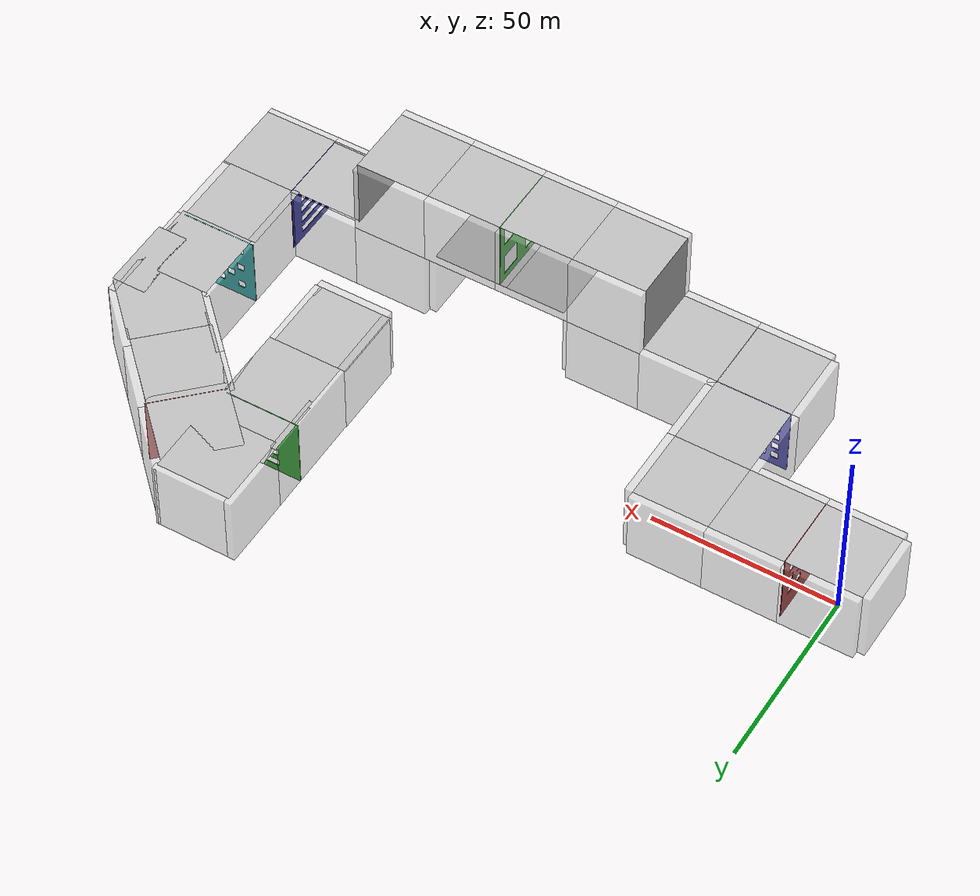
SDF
<?xml version='1.0'?>
<sdf version='1.7'>
  <model name='race_1_1'>
    <link name='link'>
      <self_collide>0</self_collide>
      <enable_wind>0</enable_wind>
      <kinematic>0</kinematic>
      <pose>0 11 10 1.5708 -0 0</pose>
      <visual name='visual'>
        <cast_shadows>1</cast_shadows>
        <transparency>0.6</transparency>
        <geometry>
          <box>
            <size>20 20 2</size>
          </box>
        </geometry>
        <material>
          <script>
            <uri>model://new_wall/materials/scripts</uri>
            <uri>model://new_wall/materials/textures/</uri>
            <name>NewWall/Image</name>
          </script>
          <shader type='pixel'/>
        </material>
        <pose>0 0 0 0 -0 0</pose>
      </visual>
      <collision name='collision'>
        <laser_retro>0</laser_retro>
        <max_contacts>10</max_contacts>
        <pose>0 0 0 0 -0 0</pose>
        <geometry>
          <box>
            <size>20 20 2</size>
          </box>
        </geometry>
        <surface>
          <friction>
            <ode>
              <mu>100</mu>
              <mu2>50</mu2>
              <fdir1>0 0 0</fdir1>
              <slip1>0</slip1>
              <slip2>0</slip2>
            </ode>
            <torsional>
              <coefficient>1</coefficient>
              <patch_radius>0</patch_radius>
              <surface_radius>0</surface_radius>
              <use_patch_radius>1</use_patch_radius>
              <ode>
                <slip>0</slip>
              </ode>
            </torsional>
          </friction>
          <bounce>
            <restitution_coefficient>0</restitution_coefficient>
            <threshold>1e+06</threshold>
          </bounce>
          <contact>
            <collide_without_contact>0</collide_without_contact>
            <collide_without_contact_bitmask>1</collide_without_contact_bitmask>
            <collide_bitmask>1</collide_bitmask>
            <ode>
              <soft_cfm>0</soft_cfm>
              <soft_erp>0.2</soft_erp>
              <kp>1e+13</kp>
              <kd>1</kd>
              <max_vel>0.01</max_vel>
              <min_depth>0</min_depth>
            </ode>
            <bullet>
              <split_impulse>1</split_impulse>
              <split_impulse_penetration_threshold>-0.01</split_impulse_penetration_threshold>
              <soft_cfm>0</soft_cfm>
              <soft_erp>0.2</soft_erp>
              <kp>1e+13</kp>
              <kd>1</kd>
            </bullet>
          </contact>
        </surface>
      </collision>
    </link>
    <link name='link_clone'>
      <self_collide>0</self_collide>
      <enable_wind>0</enable_wind>
      <kinematic>0</kinematic>
      <pose>0 -11 10 1.5708 -0 0</pose>
      <visual name='visual'>
        <cast_shadows>1</cast_shadows>
        <transparency>0.6</transparency>
        <geometry>
          <box>
            <size>20 20 2</size>
          </box>
        </geometry>
        <material>
          <script>
            <uri>model://new_wall/materials/scripts</uri>
            <uri>model://new_wall/materials/textures/</uri>
            <name>NewWall/Image</name>
          </script>
          <shader type='pixel'/>
        </material>
        <pose>0 0 0 0 -0 0</pose>
      </visual>
      <collision name='collision'>
        <laser_retro>0</laser_retro>
        <max_contacts>10</max_contacts>
        <pose>0 0 0 0 -0 0</pose>
        <geometry>
          <box>
            <size>20 20 2</size>
          </box>
        </geometry>
        <surface>
          <friction>
            <ode>
              <mu>1</mu>
              <mu2>1</mu2>
              <fdir1>0 0 0</fdir1>
              <slip1>0</slip1>
              <slip2>0</slip2>
            </ode>
            <torsional>
              <coefficient>1</coefficient>
              <patch_radius>0</patch_radius>
              <surface_radius>0</surface_radius>
              <use_patch_radius>1</use_patch_radius>
              <ode>
                <slip>0</slip>
              </ode>
            </torsional>
          </friction>
          <bounce>
            <restitution_coefficient>0</restitution_coefficient>
            <threshold>1e+06</threshold>
          </bounce>
          <contact>
            <collide_without_contact>0</collide_without_contact>
            <collide_without_contact_bitmask>1</collide_without_contact_bitmask>
            <collide_bitmask>1</collide_bitmask>
            <ode>
              <soft_cfm>0</soft_cfm>
              <soft_erp>0.2</soft_erp>
              <kp>1e+13</kp>
              <kd>1</kd>
              <max_vel>0.01</max_vel>
              <min_depth>0</min_depth>
            </ode>
            <bullet>
              <split_impulse>1</split_impulse>
              <split_impulse_penetration_threshold>-0.01</split_impulse_penetration_threshold>
              <soft_cfm>0</soft_cfm>
              <soft_erp>0.2</soft_erp>
              <kp>1e+13</kp>
              <kd>1</kd>
            </bullet>
          </contact>
        </surface>
      </collision>
    </link>
    <link name='link_clone_0'>
      <self_collide>0</self_collide>
      <enable_wind>0</enable_wind>
      <kinematic>0</kinematic>
      <pose>20 11 10 1.5708 -0 0</pose>
      <visual name='visual'>
        <cast_shadows>1</cast_shadows>
        <transparency>0.6</transparency>
        <geometry>
          <box>
            <size>20 20 2</size>
          </box>
        </geometry>
        <material>
          <script>
            <uri>model://new_wall/materials/scripts</uri>
            <uri>model://new_wall/materials/textures/</uri>
            <name>NewWall/Image</name>
          </script>
          <shader type='pixel'/>
        </material>
        <pose>0 0 0 0 -0 0</pose>
      </visual>
      <collision name='collision'>
        <laser_retro>0</laser_retro>
        <max_contacts>10</max_contacts>
        <pose>0 0 0 0 -0 0</pose>
        <geometry>
          <box>
            <size>20 20 2</size>
          </box>
        </geometry>
        <surface>
          <friction>
            <ode>
              <mu>1</mu>
              <mu2>1</mu2>
              <fdir1>0 0 0</fdir1>
              <slip1>0</slip1>
              <slip2>0</slip2>
            </ode>
            <torsional>
              <coefficient>1</coefficient>
              <patch_radius>0</patch_radius>
              <surface_radius>0</surface_radius>
              <use_patch_radius>1</use_patch_radius>
              <ode>
                <slip>0</slip>
              </ode>
            </torsional>
          </friction>
          <bounce>
            <restitution_coefficient>0</restitution_coefficient>
            <threshold>1e+06</threshold>
          </bounce>
          <contact>
            <collide_without_contact>0</collide_without_contact>
            <collide_without_contact_bitmask>1</collide_without_contact_bitmask>
            <collide_bitmask>1</collide_bitmask>
            <ode>
              <soft_cfm>0</soft_cfm>
              <soft_erp>0.2</soft_erp>
              <kp>1e+13</kp>
              <kd>1</kd>
              <max_vel>0.01</max_vel>
              <min_depth>0</min_depth>
            </ode>
            <bullet>
              <split_impulse>1</split_impulse>
              <split_impulse_penetration_threshold>-0.01</split_impulse_penetration_threshold>
              <soft_cfm>0</soft_cfm>
              <soft_erp>0.2</soft_erp>
              <kp>1e+13</kp>
              <kd>1</kd>
            </bullet>
          </contact>
        </surface>
      </collision>
    </link>
    <link name='link_clone_1'>
      <self_collide>0</self_collide>
      <enable_wind>0</enable_wind>
      <kinematic>0</kinematic>
      <pose>20 -11 10 1.5708 -0 0</pose>
      <visual name='visual'>
        <cast_shadows>1</cast_shadows>
        <transparency>0.6</transparency>
        <geometry>
          <box>
            <size>20 20 2</size>
          </box>
        </geometry>
        <material>
          <script>
            <uri>model://new_wall/materials/scripts</uri>
            <uri>model://new_wall/materials/textures/</uri>
            <name>NewWall/Image</name>
          </script>
          <shader type='pixel'/>
        </material>
        <pose>0 0 0 0 -0 0</pose>
      </visual>
      <collision name='collision'>
        <laser_retro>0</laser_retro>
        <max_contacts>10</max_contacts>
        <pose>0 0 0 0 -0 0</pose>
        <geometry>
          <box>
            <size>20 20 2</size>
          </box>
        </geometry>
        <surface>
          <friction>
            <ode>
              <mu>1</mu>
              <mu2>1</mu2>
              <fdir1>0 0 0</fdir1>
              <slip1>0</slip1>
              <slip2>0</slip2>
            </ode>
            <torsional>
              <coefficient>1</coefficient>
              <patch_radius>0</patch_radius>
              <surface_radius>0</surface_radius>
              <use_patch_radius>1</use_patch_radius>
              <ode>
                <slip>0</slip>
              </ode>
            </torsional>
          </friction>
          <bounce>
            <restitution_coefficient>0</restitution_coefficient>
            <threshold>1e+06</threshold>
          </bounce>
          <contact>
            <collide_without_contact>0</collide_without_contact>
            <collide_without_contact_bitmask>1</collide_without_contact_bitmask>
            <collide_bitmask>1</collide_bitmask>
            <ode>
              <soft_cfm>0</soft_cfm>
              <soft_erp>0.2</soft_erp>
              <kp>1e+13</kp>
              <kd>1</kd>
              <max_vel>0.01</max_vel>
              <min_depth>0</min_depth>
            </ode>
            <bullet>
              <split_impulse>1</split_impulse>
              <split_impulse_penetration_threshold>-0.01</split_impulse_penetration_threshold>
              <soft_cfm>0</soft_cfm>
              <soft_erp>0.2</soft_erp>
              <kp>1e+13</kp>
              <kd>1</kd>
            </bullet>
          </contact>
        </surface>
      </collision>
    </link>
    <link name='link_clone_10'>
      <self_collide>0</self_collide>
      <enable_wind>0</enable_wind>
      <kinematic>0</kinematic>
      <pose>100 -51 30 1.5708 -0 0</pose>
      <visual name='visual'>
        <cast_shadows>1</cast_shadows>
        <transparency>0.6</transparency>
        <geometry>
          <box>
            <size>20 20 2</size>
          </box>
        </geometry>
        <material>
          <script>
            <uri>model://new_wall/materials/scripts</uri>
            <uri>model://new_wall/materials/textures/</uri>
            <name>NewWall/Image</name>
          </script>
          <shader type='pixel'/>
        </material>
        <pose>0 0 0 0 -0 0</pose>
      </visual>
      <collision name='collision'>
        <laser_retro>0</laser_retro>
        <max_contacts>10</max_contacts>
        <pose>0 0 0 0 -0 0</pose>
        <geometry>
          <box>
            <size>20 20 2</size>
          </box>
        </geometry>
        <surface>
          <friction>
            <ode>
              <mu>1</mu>
              <mu2>1</mu2>
              <fdir1>0 0 0</fdir1>
              <slip1>0</slip1>
              <slip2>0</slip2>
            </ode>
            <torsional>
              <coefficient>1</coefficient>
              <patch_radius>0</patch_radius>
              <surface_radius>0</surface_radius>
              <use_patch_radius>1</use_patch_radius>
              <ode>
                <slip>0</slip>
              </ode>
            </torsional>
          </friction>
          <bounce>
            <restitution_coefficient>0</restitution_coefficient>
            <threshold>1e+06</threshold>
          </bounce>
          <contact>
            <collide_without_contact>0</collide_without_contact>
            <collide_without_contact_bitmask>1</collide_without_contact_bitmask>
            <collide_bitmask>1</collide_bitmask>
            <ode>
              <soft_cfm>0</soft_cfm>
              <soft_erp>0.2</soft_erp>
              <kp>1e+13</kp>
              <kd>1</kd>
              <max_vel>0.01</max_vel>
              <min_depth>0</min_depth>
            </ode>
            <bullet>
              <split_impulse>1</split_impulse>
              <split_impulse_penetration_threshold>-0.01</split_impulse_penetration_threshold>
              <soft_cfm>0</soft_cfm>
              <soft_erp>0.2</soft_erp>
              <kp>1e+13</kp>
              <kd>1</kd>
            </bullet>
          </contact>
        </surface>
      </collision>
    </link>
    <link name='link_clone_10_clone'>
      <self_collide>0</self_collide>
      <enable_wind>0</enable_wind>
      <kinematic>0</kinematic>
      <pose>120 -51 30 1.5708 -0 0</pose>
      <visual name='visual'>
        <cast_shadows>1</cast_shadows>
        <transparency>0.6</transparency>
        <geometry>
          <box>
            <size>20 20 2</size>
          </box>
        </geometry>
        <material>
          <script>
            <uri>model://new_wall/materials/scripts</uri>
            <uri>model://new_wall/materials/textures/</uri>
            <name>NewWall/Image</name>
          </script>
          <shader type='pixel'/>
        </material>
        <pose>0 0 0 0 -0 0</pose>
      </visual>
      <collision name='collision'>
        <laser_retro>0</laser_retro>
        <max_contacts>10</max_contacts>
        <pose>0 0 0 0 -0 0</pose>
        <geometry>
          <box>
            <size>20 20 2</size>
          </box>
        </geometry>
        <surface>
          <friction>
            <ode>
              <mu>1</mu>
              <mu2>1</mu2>
              <fdir1>0 0 0</fdir1>
              <slip1>0</slip1>
              <slip2>0</slip2>
            </ode>
            <torsional>
              <coefficient>1</coefficient>
              <patch_radius>0</patch_radius>
              <surface_radius>0</surface_radius>
              <use_patch_radius>1</use_patch_radius>
              <ode>
                <slip>0</slip>
              </ode>
            </torsional>
          </friction>
          <bounce>
            <restitution_coefficient>0</restitution_coefficient>
            <threshold>1e+06</threshold>
          </bounce>
          <contact>
            <collide_without_contact>0</collide_without_contact>
            <collide_without_contact_bitmask>1</collide_without_contact_bitmask>
            <collide_bitmask>1</collide_bitmask>
            <ode>
              <soft_cfm>0</soft_cfm>
              <soft_erp>0.2</soft_erp>
              <kp>1e+13</kp>
              <kd>1</kd>
              <max_vel>0.01</max_vel>
              <min_depth>0</min_depth>
            </ode>
            <bullet>
              <split_impulse>1</split_impulse>
              <split_impulse_penetration_threshold>-0.01</split_impulse_penetration_threshold>
              <soft_cfm>0</soft_cfm>
              <soft_erp>0.2</soft_erp>
              <kp>1e+13</kp>
              <kd>1</kd>
            </bullet>
          </contact>
        </surface>
      </collision>
    </link>
    <link name='link_clone_10_clone_0'>
      <self_collide>0</self_collide>
      <enable_wind>0</enable_wind>
      <kinematic>0</kinematic>
      <pose>100 -29 30 1.5708 -0 0</pose>
      <visual name='visual'>
        <cast_shadows>1</cast_shadows>
        <transparency>0.6</transparency>
        <geometry>
          <box>
            <size>20 20 2</size>
          </box>
        </geometry>
        <material>
          <script>
            <uri>model://new_wall/materials/scripts</uri>
            <uri>model://new_wall/materials/textures/</uri>
            <name>NewWall/Image</name>
          </script>
          <shader type='pixel'/>
        </material>
        <pose>0 0 0 0 -0 0</pose>
      </visual>
      <collision name='collision'>
        <laser_retro>0</laser_retro>
        <max_contacts>10</max_contacts>
        <pose>0 0 0 0 -0 0</pose>
        <geometry>
          <box>
            <size>20 20 2</size>
          </box>
        </geometry>
        <surface>
          <friction>
            <ode>
              <mu>1</mu>
              <mu2>1</mu2>
              <fdir1>0 0 0</fdir1>
              <slip1>0</slip1>
              <slip2>0</slip2>
            </ode>
            <torsional>
              <coefficient>1</coefficient>
              <patch_radius>0</patch_radius>
              <surface_radius>0</surface_radius>
              <use_patch_radius>1</use_patch_radius>
              <ode>
                <slip>0</slip>
              </ode>
            </torsional>
          </friction>
          <bounce>
            <restitution_coefficient>0</restitution_coefficient>
            <threshold>1e+06</threshold>
          </bounce>
          <contact>
            <collide_without_contact>0</collide_without_contact>
            <collide_without_contact_bitmask>1</collide_without_contact_bitmask>
            <collide_bitmask>1</collide_bitmask>
            <ode>
              <soft_cfm>0</soft_cfm>
              <soft_erp>0.2</soft_erp>
              <kp>1e+13</kp>
              <kd>1</kd>
              <max_vel>0.01</max_vel>
              <min_depth>0</min_depth>
            </ode>
            <bullet>
              <split_impulse>1</split_impulse>
              <split_impulse_penetration_threshold>-0.01</split_impulse_penetration_threshold>
              <soft_cfm>0</soft_cfm>
              <soft_erp>0.2</soft_erp>
              <kp>1e+13</kp>
              <kd>1</kd>
            </bullet>
          </contact>
        </surface>
      </collision>
    </link>
    <link name='link_clone_10_clone_1'>
      <self_collide>0</self_collide>
      <enable_wind>0</enable_wind>
      <kinematic>0</kinematic>
      <pose>120 -29 30 1.5708 -0 0</pose>
      <visual name='visual'>
        <cast_shadows>1</cast_shadows>
        <transparency>0.6</transparency>
        <geometry>
          <box>
            <size>20 20 2</size>
          </box>
        </geometry>
        <material>
          <script>
            <uri>model://new_wall/materials/scripts</uri>
            <uri>model://new_wall/materials/textures/</uri>
            <name>NewWall/Image</name>
          </script>
          <shader type='pixel'/>
        </material>
        <pose>0 0 0 0 -0 0</pose>
      </visual>
      <collision name='collision'>
        <laser_retro>0</laser_retro>
        <max_contacts>10</max_contacts>
        <pose>0 0 0 0 -0 0</pose>
        <geometry>
          <box>
            <size>20 20 2</size>
          </box>
        </geometry>
        <surface>
          <friction>
            <ode>
              <mu>1</mu>
              <mu2>1</mu2>
              <fdir1>0 0 0</fdir1>
              <slip1>0</slip1>
              <slip2>0</slip2>
            </ode>
            <torsional>
              <coefficient>1</coefficient>
              <patch_radius>0</patch_radius>
              <surface_radius>0</surface_radius>
              <use_patch_radius>1</use_patch_radius>
              <ode>
                <slip>0</slip>
              </ode>
            </torsional>
          </friction>
          <bounce>
            <restitution_coefficient>0</restitution_coefficient>
            <threshold>1e+06</threshold>
          </bounce>
          <contact>
            <collide_without_contact>0</collide_without_contact>
            <collide_without_contact_bitmask>1</collide_without_contact_bitmask>
            <collide_bitmask>1</collide_bitmask>
            <ode>
              <soft_cfm>0</soft_cfm>
              <soft_erp>0.2</soft_erp>
              <kp>1e+13</kp>
              <kd>1</kd>
              <max_vel>0.01</max_vel>
              <min_depth>0</min_depth>
            </ode>
            <bullet>
              <split_impulse>1</split_impulse>
              <split_impulse_penetration_threshold>-0.01</split_impulse_penetration_threshold>
              <soft_cfm>0</soft_cfm>
              <soft_erp>0.2</soft_erp>
              <kp>1e+13</kp>
              <kd>1</kd>
            </bullet>
          </contact>
        </surface>
      </collision>
    </link>
    <link name='link_clone_10_clone_2'>
      <self_collide>0</self_collide>
      <enable_wind>0</enable_wind>
      <kinematic>0</kinematic>
      <pose>80 -51 30 1.5708 -0 0</pose>
      <visual name='visual'>
        <cast_shadows>1</cast_shadows>
        <transparency>0.6</transparency>
        <geometry>
          <box>
            <size>20 20 2</size>
          </box>
        </geometry>
        <material>
          <script>
            <uri>model://new_wall/materials/scripts</uri>
            <uri>model://new_wall/materials/textures/</uri>
            <name>NewWall/Image</name>
          </script>
          <shader type='pixel'/>
        </material>
        <pose>0 0 0 0 -0 0</pose>
      </visual>
      <collision name='collision'>
        <laser_retro>0</laser_retro>
        <max_contacts>10</max_contacts>
        <pose>0 0 0 0 -0 0</pose>
        <geometry>
          <box>
            <size>20 20 2</size>
          </box>
        </geometry>
        <surface>
          <friction>
            <ode>
              <mu>1</mu>
              <mu2>1</mu2>
              <fdir1>0 0 0</fdir1>
              <slip1>0</slip1>
              <slip2>0</slip2>
            </ode>
            <torsional>
              <coefficient>1</coefficient>
              <patch_radius>0</patch_radius>
              <surface_radius>0</surface_radius>
              <use_patch_radius>1</use_patch_radius>
              <ode>
                <slip>0</slip>
              </ode>
            </torsional>
          </friction>
          <bounce>
            <restitution_coefficient>0</restitution_coefficient>
            <threshold>1e+06</threshold>
          </bounce>
          <contact>
            <collide_without_contact>0</collide_without_contact>
            <collide_without_contact_bitmask>1</collide_without_contact_bitmask>
            <collide_bitmask>1</collide_bitmask>
            <ode>
              <soft_cfm>0</soft_cfm>
              <soft_erp>0.2</soft_erp>
              <kp>1e+13</kp>
              <kd>1</kd>
              <max_vel>0.01</max_vel>
              <min_depth>0</min_depth>
            </ode>
            <bullet>
              <split_impulse>1</split_impulse>
              <split_impulse_penetration_threshold>-0.01</split_impulse_penetration_threshold>
              <soft_cfm>0</soft_cfm>
              <soft_erp>0.2</soft_erp>
              <kp>1e+13</kp>
              <kd>1</kd>
            </bullet>
          </contact>
        </surface>
      </collision>
    </link>
    <link name='link_clone_10_clone_3'>
      <self_collide>0</self_collide>
      <enable_wind>0</enable_wind>
      <kinematic>0</kinematic>
      <pose>140 -51 30 1.5708 -0 0</pose>
      <visual name='visual'>
        <cast_shadows>1</cast_shadows>
        <transparency>0.6</transparency>
        <geometry>
          <box>
            <size>20 20 2</size>
          </box>
        </geometry>
        <material>
          <script>
            <uri>model://new_wall/materials/scripts</uri>
            <uri>model://new_wall/materials/textures/</uri>
            <name>NewWall/Image</name>
          </script>
          <shader type='pixel'/>
        </material>
        <pose>0 0 0 0 -0 0</pose>
      </visual>
      <collision name='collision'>
        <laser_retro>0</laser_retro>
        <max_contacts>10</max_contacts>
        <pose>0 0 0 0 -0 0</pose>
        <geometry>
          <box>
            <size>20 20 2</size>
          </box>
        </geometry>
        <surface>
          <friction>
            <ode>
              <mu>1</mu>
              <mu2>1</mu2>
              <fdir1>0 0 0</fdir1>
              <slip1>0</slip1>
              <slip2>0</slip2>
            </ode>
            <torsional>
              <coefficient>1</coefficient>
              <patch_radius>0</patch_radius>
              <surface_radius>0</surface_radius>
              <use_patch_radius>1</use_patch_radius>
              <ode>
                <slip>0</slip>
              </ode>
            </torsional>
          </friction>
          <bounce>
            <restitution_coefficient>0</restitution_coefficient>
            <threshold>1e+06</threshold>
          </bounce>
          <contact>
            <collide_without_contact>0</collide_without_contact>
            <collide_without_contact_bitmask>1</collide_without_contact_bitmask>
            <collide_bitmask>1</collide_bitmask>
            <ode>
              <soft_cfm>0</soft_cfm>
              <soft_erp>0.2</soft_erp>
              <kp>1e+13</kp>
              <kd>1</kd>
              <max_vel>0.01</max_vel>
              <min_depth>0</min_depth>
            </ode>
            <bullet>
              <split_impulse>1</split_impulse>
              <split_impulse_penetration_threshold>-0.01</split_impulse_penetration_threshold>
              <soft_cfm>0</soft_cfm>
              <soft_erp>0.2</soft_erp>
              <kp>1e+13</kp>
              <kd>1</kd>
            </bullet>
          </contact>
        </surface>
      </collision>
    </link>
    <link name='link_clone_10_clone_4'>
      <self_collide>0</self_collide>
      <enable_wind>0</enable_wind>
      <kinematic>0</kinematic>
      <pose>80 -29 30 1.5708 -0 0</pose>
      <visual name='visual'>
        <cast_shadows>1</cast_shadows>
        <transparency>0.6</transparency>
        <geometry>
          <box>
            <size>20 20 2</size>
          </box>
        </geometry>
        <material>
          <script>
            <uri>model://new_wall/materials/scripts</uri>
            <uri>model://new_wall/materials/textures/</uri>
            <name>NewWall/Image</name>
          </script>
          <shader type='pixel'/>
        </material>
        <pose>0 0 0 0 -0 0</pose>
      </visual>
      <collision name='collision'>
        <laser_retro>0</laser_retro>
        <max_contacts>10</max_contacts>
        <pose>0 0 0 0 -0 0</pose>
        <geometry>
          <box>
            <size>20 20 2</size>
          </box>
        </geometry>
        <surface>
          <friction>
            <ode>
              <mu>1</mu>
              <mu2>1</mu2>
              <fdir1>0 0 0</fdir1>
              <slip1>0</slip1>
              <slip2>0</slip2>
            </ode>
            <torsional>
              <coefficient>1</coefficient>
              <patch_radius>0</patch_radius>
              <surface_radius>0</surface_radius>
              <use_patch_radius>1</use_patch_radius>
              <ode>
                <slip>0</slip>
              </ode>
            </torsional>
          </friction>
          <bounce>
            <restitution_coefficient>0</restitution_coefficient>
            <threshold>1e+06</threshold>
          </bounce>
          <contact>
            <collide_without_contact>0</collide_without_contact>
            <collide_without_contact_bitmask>1</collide_without_contact_bitmask>
            <collide_bitmask>1</collide_bitmask>
            <ode>
              <soft_cfm>0</soft_cfm>
              <soft_erp>0.2</soft_erp>
              <kp>1e+13</kp>
              <kd>1</kd>
              <max_vel>0.01</max_vel>
              <min_depth>0</min_depth>
            </ode>
            <bullet>
              <split_impulse>1</split_impulse>
              <split_impulse_penetration_threshold>-0.01</split_impulse_penetration_threshold>
              <soft_cfm>0</soft_cfm>
              <soft_erp>0.2</soft_erp>
              <kp>1e+13</kp>
              <kd>1</kd>
            </bullet>
          </contact>
        </surface>
      </collision>
    </link>
    <link name='link_clone_10_clone_5'>
      <self_collide>0</self_collide>
      <enable_wind>0</enable_wind>
      <kinematic>0</kinematic>
      <pose>140 -29 30 1.5708 -0 0</pose>
      <visual name='visual'>
        <cast_shadows>1</cast_shadows>
        <transparency>0.6</transparency>
        <geometry>
          <box>
            <size>20 20 2</size>
          </box>
        </geometry>
        <material>
          <script>
            <uri>model://new_wall/materials/scripts</uri>
            <uri>model://new_wall/materials/textures/</uri>
            <name>NewWall/Image</name>
          </script>
          <shader type='pixel'/>
        </material>
        <pose>0 0 0 0 -0 0</pose>
      </visual>
      <collision name='collision'>
        <laser_retro>0</laser_retro>
        <max_contacts>10</max_contacts>
        <pose>0 0 0 0 -0 0</pose>
        <geometry>
          <box>
            <size>20 20 2</size>
          </box>
        </geometry>
        <surface>
          <friction>
            <ode>
              <mu>1</mu>
              <mu2>1</mu2>
              <fdir1>0 0 0</fdir1>
              <slip1>0</slip1>
              <slip2>0</slip2>
            </ode>
            <torsional>
              <coefficient>1</coefficient>
              <patch_radius>0</patch_radius>
              <surface_radius>0</surface_radius>
              <use_patch_radius>1</use_patch_radius>
              <ode>
                <slip>0</slip>
              </ode>
            </torsional>
          </friction>
          <bounce>
            <restitution_coefficient>0</restitution_coefficient>
            <threshold>1e+06</threshold>
          </bounce>
          <contact>
            <collide_without_contact>0</collide_without_contact>
            <collide_without_contact_bitmask>1</collide_without_contact_bitmask>
            <collide_bitmask>1</collide_bitmask>
            <ode>
              <soft_cfm>0</soft_cfm>
              <soft_erp>0.2</soft_erp>
              <kp>1e+13</kp>
              <kd>1</kd>
              <max_vel>0.01</max_vel>
              <min_depth>0</min_depth>
            </ode>
            <bullet>
              <split_impulse>1</split_impulse>
              <split_impulse_penetration_threshold>-0.01</split_impulse_penetration_threshold>
              <soft_cfm>0</soft_cfm>
              <soft_erp>0.2</soft_erp>
              <kp>1e+13</kp>
              <kd>1</kd>
            </bullet>
          </contact>
        </surface>
      </collision>
    </link>
    <link name='link_clone_12'>
      <self_collide>0</self_collide>
      <enable_wind>0</enable_wind>
      <kinematic>0</kinematic>
      <pose>140 -29 10 1.5708 -0 0</pose>
      <visual name='visual'>
        <cast_shadows>1</cast_shadows>
        <transparency>0.6</transparency>
        <geometry>
          <box>
            <size>20 20 2</size>
          </box>
        </geometry>
        <material>
          <script>
            <uri>model://new_wall/materials/scripts</uri>
            <uri>model://new_wall/materials/textures/</uri>
            <name>NewWall/Image</name>
          </script>
          <shader type='pixel'/>
        </material>
        <pose>0 0 0 0 -0 0</pose>
      </visual>
      <collision name='collision'>
        <laser_retro>0</laser_retro>
        <max_contacts>10</max_contacts>
        <pose>0 0 0 0 -0 0</pose>
        <geometry>
          <box>
            <size>20 20 2</size>
          </box>
        </geometry>
        <surface>
          <friction>
            <ode>
              <mu>1</mu>
              <mu2>1</mu2>
              <fdir1>0 0 0</fdir1>
              <slip1>0</slip1>
              <slip2>0</slip2>
            </ode>
            <torsional>
              <coefficient>1</coefficient>
              <patch_radius>0</patch_radius>
              <surface_radius>0</surface_radius>
              <use_patch_radius>1</use_patch_radius>
              <ode>
                <slip>0</slip>
              </ode>
            </torsional>
          </friction>
          <bounce>
            <restitution_coefficient>0</restitution_coefficient>
            <threshold>1e+06</threshold>
          </bounce>
          <contact>
            <collide_without_contact>0</collide_without_contact>
            <collide_without_contact_bitmask>1</collide_without_contact_bitmask>
            <collide_bitmask>1</collide_bitmask>
            <ode>
              <soft_cfm>0</soft_cfm>
              <soft_erp>0.2</soft_erp>
              <kp>1e+13</kp>
              <kd>1</kd>
              <max_vel>0.01</max_vel>
              <min_depth>0</min_depth>
            </ode>
            <bullet>
              <split_impulse>1</split_impulse>
              <split_impulse_penetration_threshold>-0.01</split_impulse_penetration_threshold>
              <soft_cfm>0</soft_cfm>
              <soft_erp>0.2</soft_erp>
              <kp>1e+13</kp>
              <kd>1</kd>
            </bullet>
          </contact>
        </surface>
      </collision>
    </link>
    <link name='link_clone_13'>
      <self_collide>0</self_collide>
      <enable_wind>0</enable_wind>
      <kinematic>0</kinematic>
      <pose>160 -29 10 1.5708 -0 0</pose>
      <visual name='visual'>
        <cast_shadows>1</cast_shadows>
        <transparency>0.6</transparency>
        <geometry>
          <box>
            <size>20 20 2</size>
          </box>
        </geometry>
        <material>
          <script>
            <uri>model://new_wall/materials/scripts</uri>
            <uri>model://new_wall/materials/textures/</uri>
            <name>NewWall/Image</name>
          </script>
          <shader type='pixel'/>
        </material>
        <pose>0 0 0 0 -0 0</pose>
      </visual>
      <collision name='collision'>
        <laser_retro>0</laser_retro>
        <max_contacts>10</max_contacts>
        <pose>0 0 0 0 -0 0</pose>
        <geometry>
          <box>
            <size>20 20 2</size>
          </box>
        </geometry>
        <surface>
          <friction>
            <ode>
              <mu>1</mu>
              <mu2>1</mu2>
              <fdir1>0 0 0</fdir1>
              <slip1>0</slip1>
              <slip2>0</slip2>
            </ode>
            <torsional>
              <coefficient>1</coefficient>
              <patch_radius>0</patch_radius>
              <surface_radius>0</surface_radius>
              <use_patch_radius>1</use_patch_radius>
              <ode>
                <slip>0</slip>
              </ode>
            </torsional>
          </friction>
          <bounce>
            <restitution_coefficient>0</restitution_coefficient>
            <threshold>1e+06</threshold>
          </bounce>
          <contact>
            <collide_without_contact>0</collide_without_contact>
            <collide_without_contact_bitmask>1</collide_without_contact_bitmask>
            <collide_bitmask>1</collide_bitmask>
            <ode>
              <soft_cfm>0</soft_cfm>
              <soft_erp>0.2</soft_erp>
              <kp>1e+13</kp>
              <kd>1</kd>
              <max_vel>0.01</max_vel>
              <min_depth>0</min_depth>
            </ode>
            <bullet>
              <split_impulse>1</split_impulse>
              <split_impulse_penetration_threshold>-0.01</split_impulse_penetration_threshold>
              <soft_cfm>0</soft_cfm>
              <soft_erp>0.2</soft_erp>
              <kp>1e+13</kp>
              <kd>1</kd>
            </bullet>
          </contact>
        </surface>
      </collision>
    </link>
    <link name='link_clone_14'>
      <self_collide>0</self_collide>
      <enable_wind>0</enable_wind>
      <kinematic>0</kinematic>
      <pose>140 -51 10 1.5708 -0 0</pose>
      <visual name='visual'>
        <cast_shadows>1</cast_shadows>
        <transparency>0.6</transparency>
        <geometry>
          <box>
            <size>20 20 2</size>
          </box>
        </geometry>
        <material>
          <script>
            <uri>model://new_wall/materials/scripts</uri>
            <uri>model://new_wall/materials/textures/</uri>
            <name>NewWall/Image</name>
          </script>
          <shader type='pixel'/>
        </material>
        <pose>0 0 0 0 -0 0</pose>
      </visual>
      <collision name='collision'>
        <laser_retro>0</laser_retro>
        <max_contacts>10</max_contacts>
        <pose>0 0 0 0 -0 0</pose>
        <geometry>
          <box>
            <size>20 20 2</size>
          </box>
        </geometry>
        <surface>
          <friction>
            <ode>
              <mu>1</mu>
              <mu2>1</mu2>
              <fdir1>0 0 0</fdir1>
              <slip1>0</slip1>
              <slip2>0</slip2>
            </ode>
            <torsional>
              <coefficient>1</coefficient>
              <patch_radius>0</patch_radius>
              <surface_radius>0</surface_radius>
              <use_patch_radius>1</use_patch_radius>
              <ode>
                <slip>0</slip>
              </ode>
            </torsional>
          </friction>
          <bounce>
            <restitution_coefficient>0</restitution_coefficient>
            <threshold>1e+06</threshold>
          </bounce>
          <contact>
            <collide_without_contact>0</collide_without_contact>
            <collide_without_contact_bitmask>1</collide_without_contact_bitmask>
            <collide_bitmask>1</collide_bitmask>
            <ode>
              <soft_cfm>0</soft_cfm>
              <soft_erp>0.2</soft_erp>
              <kp>1e+13</kp>
              <kd>1</kd>
              <max_vel>0.01</max_vel>
              <min_depth>0</min_depth>
            </ode>
            <bullet>
              <split_impulse>1</split_impulse>
              <split_impulse_penetration_threshold>-0.01</split_impulse_penetration_threshold>
              <soft_cfm>0</soft_cfm>
              <soft_erp>0.2</soft_erp>
              <kp>1e+13</kp>
              <kd>1</kd>
            </bullet>
          </contact>
        </surface>
      </collision>
    </link>
    <link name='link_clone_15'>
      <self_collide>0</self_collide>
      <enable_wind>0</enable_wind>
      <kinematic>0</kinematic>
      <pose>160 -51 10 1.5708 -0 0</pose>
      <visual name='visual'>
        <cast_shadows>1</cast_shadows>
        <transparency>0.6</transparency>
        <geometry>
          <box>
            <size>20 20 2</size>
          </box>
        </geometry>
        <material>
          <script>
            <uri>model://new_wall/materials/scripts</uri>
            <uri>model://new_wall/materials/textures/</uri>
            <name>NewWall/Image</name>
          </script>
          <shader type='pixel'/>
        </material>
        <pose>0 0 0 0 -0 0</pose>
      </visual>
      <collision name='collision'>
        <laser_retro>0</laser_retro>
        <max_contacts>10</max_contacts>
        <pose>0 0 0 0 -0 0</pose>
        <geometry>
          <box>
            <size>20 20 2</size>
          </box>
        </geometry>
        <surface>
          <friction>
            <ode>
              <mu>1</mu>
              <mu2>1</mu2>
              <fdir1>0 0 0</fdir1>
              <slip1>0</slip1>
              <slip2>0</slip2>
            </ode>
            <torsional>
              <coefficient>1</coefficient>
              <patch_radius>0</patch_radius>
              <surface_radius>0</surface_radius>
              <use_patch_radius>1</use_patch_radius>
              <ode>
                <slip>0</slip>
              </ode>
            </torsional>
          </friction>
          <bounce>
            <restitution_coefficient>0</restitution_coefficient>
            <threshold>1e+06</threshold>
          </bounce>
          <contact>
            <collide_without_contact>0</collide_without_contact>
            <collide_without_contact_bitmask>1</collide_without_contact_bitmask>
            <collide_bitmask>1</collide_bitmask>
            <ode>
              <soft_cfm>0</soft_cfm>
              <soft_erp>0.2</soft_erp>
              <kp>1e+13</kp>
              <kd>1</kd>
              <max_vel>0.01</max_vel>
              <min_depth>0</min_depth>
            </ode>
            <bullet>
              <split_impulse>1</split_impulse>
              <split_impulse_penetration_threshold>-0.01</split_impulse_penetration_threshold>
              <soft_cfm>0</soft_cfm>
              <soft_erp>0.2</soft_erp>
              <kp>1e+13</kp>
              <kd>1</kd>
            </bullet>
          </contact>
        </surface>
      </collision>
    </link>
    <link name='link_clone_17'>
      <self_collide>0</self_collide>
      <enable_wind>0</enable_wind>
      <kinematic>0</kinematic>
      <pose>180 -51 10 1.5708 -0 0</pose>
      <visual name='visual'>
        <cast_shadows>1</cast_shadows>
        <transparency>0.6</transparency>
        <geometry>
          <box>
            <size>20 20 2</size>
          </box>
        </geometry>
        <material>
          <script>
            <uri>model://new_wall/materials/scripts</uri>
            <uri>model://new_wall/materials/textures/</uri>
            <name>NewWall/Image</name>
          </script>
          <shader type='pixel'/>
        </material>
        <pose>0 0 0 0 -0 0</pose>
      </visual>
      <collision name='collision'>
        <laser_retro>0</laser_retro>
        <max_contacts>10</max_contacts>
        <pose>0 0 0 0 -0 0</pose>
        <geometry>
          <box>
            <size>20 20 2</size>
          </box>
        </geometry>
        <surface>
          <friction>
            <ode>
              <mu>1</mu>
              <mu2>1</mu2>
              <fdir1>0 0 0</fdir1>
              <slip1>0</slip1>
              <slip2>0</slip2>
            </ode>
            <torsional>
              <coefficient>1</coefficient>
              <patch_radius>0</patch_radius>
              <surface_radius>0</surface_radius>
              <use_patch_radius>1</use_patch_radius>
              <ode>
                <slip>0</slip>
              </ode>
            </torsional>
          </friction>
          <bounce>
            <restitution_coefficient>0</restitution_coefficient>
            <threshold>1e+06</threshold>
          </bounce>
          <contact>
            <collide_without_contact>0</collide_without_contact>
            <collide_without_contact_bitmask>1</collide_without_contact_bitmask>
            <collide_bitmask>1</collide_bitmask>
            <ode>
              <soft_cfm>0</soft_cfm>
              <soft_erp>0.2</soft_erp>
              <kp>1e+13</kp>
              <kd>1</kd>
              <max_vel>0.01</max_vel>
              <min_depth>0</min_depth>
            </ode>
            <bullet>
              <split_impulse>1</split_impulse>
              <split_impulse_penetration_threshold>-0.01</split_impulse_penetration_threshold>
              <soft_cfm>0</soft_cfm>
              <soft_erp>0.2</soft_erp>
              <kp>1e+13</kp>
              <kd>1</kd>
            </bullet>
          </contact>
        </surface>
      </collision>
    </link>
    <link name='link_clone_18'>
      <self_collide>0</self_collide>
      <enable_wind>0</enable_wind>
      <kinematic>0</kinematic>
      <pose>182.482 26 10 1.5708 3e-06 -0.785398</pose>
      <visual name='visual'>
        <cast_shadows>1</cast_shadows>
        <transparency>0.6</transparency>
        <geometry>
          <box>
            <size>20 20 2</size>
          </box>
        </geometry>
        <material>
          <script>
            <uri>model://new_wall/materials/scripts</uri>
            <uri>model://new_wall/materials/textures/</uri>
            <name>NewWall/Image</name>
          </script>
          <shader type='pixel'/>
        </material>
        <pose>0 0 0 0 -0 0</pose>
      </visual>
      <collision name='collision'>
        <laser_retro>0</laser_retro>
        <max_contacts>10</max_contacts>
        <pose>0 0 0 0 -0 0</pose>
        <geometry>
          <box>
            <size>20 20 2</size>
          </box>
        </geometry>
        <surface>
          <friction>
            <ode>
              <mu>1</mu>
              <mu2>1</mu2>
              <fdir1>0 0 0</fdir1>
              <slip1>0</slip1>
              <slip2>0</slip2>
            </ode>
            <torsional>
              <coefficient>1</coefficient>
              <patch_radius>0</patch_radius>
              <surface_radius>0</surface_radius>
              <use_patch_radius>1</use_patch_radius>
              <ode>
                <slip>0</slip>
              </ode>
            </torsional>
          </friction>
          <bounce>
            <restitution_coefficient>0</restitution_coefficient>
            <threshold>1e+06</threshold>
          </bounce>
          <contact>
            <collide_without_contact>0</collide_without_contact>
            <collide_without_contact_bitmask>1</collide_without_contact_bitmask>
            <collide_bitmask>1</collide_bitmask>
            <ode>
              <soft_cfm>0</soft_cfm>
              <soft_erp>0.2</soft_erp>
              <kp>1e+13</kp>
              <kd>1</kd>
              <max_vel>0.01</max_vel>
              <min_depth>0</min_depth>
            </ode>
            <bullet>
              <split_impulse>1</split_impulse>
              <split_impulse_penetration_threshold>-0.01</split_impulse_penetration_threshold>
              <soft_cfm>0</soft_cfm>
              <soft_erp>0.2</soft_erp>
              <kp>1e+13</kp>
              <kd>1</kd>
            </bullet>
          </contact>
        </surface>
      </collision>
    </link>
    <link name='link_clone_18_clone'>
      <self_collide>0</self_collide>
      <enable_wind>0</enable_wind>
      <kinematic>0</kinematic>
      <pose>162.585 16 10 1.5708 3e-06 -0.785398</pose>
      <visual name='visual'>
        <cast_shadows>1</cast_shadows>
        <transparency>0.6</transparency>
        <geometry>
          <box>
            <size>20 20 2</size>
          </box>
        </geometry>
        <material>
          <script>
            <uri>model://new_wall/materials/scripts</uri>
            <uri>model://new_wall/materials/textures/</uri>
            <name>NewWall/Image</name>
          </script>
          <shader type='pixel'/>
        </material>
        <pose>0 0 0 0 -0 0</pose>
      </visual>
      <collision name='collision'>
        <laser_retro>0</laser_retro>
        <max_contacts>10</max_contacts>
        <pose>0 0 0 0 -0 0</pose>
        <geometry>
          <box>
            <size>20 20 2</size>
          </box>
        </geometry>
        <surface>
          <friction>
            <ode>
              <mu>1</mu>
              <mu2>1</mu2>
              <fdir1>0 0 0</fdir1>
              <slip1>0</slip1>
              <slip2>0</slip2>
            </ode>
            <torsional>
              <coefficient>1</coefficient>
              <patch_radius>0</patch_radius>
              <surface_radius>0</surface_radius>
              <use_patch_radius>1</use_patch_radius>
              <ode>
                <slip>0</slip>
              </ode>
            </torsional>
          </friction>
          <bounce>
            <restitution_coefficient>0</restitution_coefficient>
            <threshold>1e+06</threshold>
          </bounce>
          <contact>
            <collide_without_contact>0</collide_without_contact>
            <collide_without_contact_bitmask>1</collide_without_contact_bitmask>
            <collide_bitmask>1</collide_bitmask>
            <ode>
              <soft_cfm>0</soft_cfm>
              <soft_erp>0.2</soft_erp>
              <kp>1e+13</kp>
              <kd>1</kd>
              <max_vel>0.01</max_vel>
              <min_depth>0</min_depth>
            </ode>
            <bullet>
              <split_impulse>1</split_impulse>
              <split_impulse_penetration_threshold>-0.01</split_impulse_penetration_threshold>
              <soft_cfm>0</soft_cfm>
              <soft_erp>0.2</soft_erp>
              <kp>1e+13</kp>
              <kd>1</kd>
            </bullet>
          </contact>
        </surface>
      </collision>
    </link>
    <link name='link_clone_18_clone_0'>
      <self_collide>0</self_collide>
      <enable_wind>0</enable_wind>
      <kinematic>0</kinematic>
      <pose>168.495 40 10 1.5708 3e-06 -0.785398</pose>
      <visual name='visual'>
        <cast_shadows>1</cast_shadows>
        <transparency>0.6</transparency>
        <geometry>
          <box>
            <size>20 20 2</size>
          </box>
        </geometry>
        <material>
          <script>
            <uri>model://new_wall/materials/scripts</uri>
            <uri>model://new_wall/materials/textures/</uri>
            <name>NewWall/Image</name>
          </script>
          <shader type='pixel'/>
        </material>
        <pose>0 0 0 0 -0 0</pose>
      </visual>
      <collision name='collision'>
        <laser_retro>0</laser_retro>
        <max_contacts>10</max_contacts>
        <pose>0 0 0 0 -0 0</pose>
        <geometry>
          <box>
            <size>20 20 2</size>
          </box>
        </geometry>
        <surface>
          <friction>
            <ode>
              <mu>1</mu>
              <mu2>1</mu2>
              <fdir1>0 0 0</fdir1>
              <slip1>0</slip1>
              <slip2>0</slip2>
            </ode>
            <torsional>
              <coefficient>1</coefficient>
              <patch_radius>0</patch_radius>
              <surface_radius>0</surface_radius>
              <use_patch_radius>1</use_patch_radius>
              <ode>
                <slip>0</slip>
              </ode>
            </torsional>
          </friction>
          <bounce>
            <restitution_coefficient>0</restitution_coefficient>
            <threshold>1e+06</threshold>
          </bounce>
          <contact>
            <collide_without_contact>0</collide_without_contact>
            <collide_without_contact_bitmask>1</collide_without_contact_bitmask>
            <collide_bitmask>1</collide_bitmask>
            <ode>
              <soft_cfm>0</soft_cfm>
              <soft_erp>0.2</soft_erp>
              <kp>1e+13</kp>
              <kd>1</kd>
              <max_vel>0.01</max_vel>
              <min_depth>0</min_depth>
            </ode>
            <bullet>
              <split_impulse>1</split_impulse>
              <split_impulse_penetration_threshold>-0.01</split_impulse_penetration_threshold>
              <soft_cfm>0</soft_cfm>
              <soft_erp>0.2</soft_erp>
              <kp>1e+13</kp>
              <kd>1</kd>
            </bullet>
          </contact>
        </surface>
      </collision>
    </link>
    <link name='link_clone_18_clone_1'>
      <self_collide>0</self_collide>
      <enable_wind>0</enable_wind>
      <kinematic>0</kinematic>
      <pose>153.586 25 10 1.5708 3e-06 -0.785398</pose>
      <visual name='visual'>
        <cast_shadows>1</cast_shadows>
        <transparency>0.6</transparency>
        <geometry>
          <box>
            <size>20 20 2</size>
          </box>
        </geometry>
        <material>
          <script>
            <uri>model://new_wall/materials/scripts</uri>
            <uri>model://new_wall/materials/textures/</uri>
            <name>NewWall/Image</name>
          </script>
          <shader type='pixel'/>
        </material>
        <pose>0 0 0 0 -0 0</pose>
      </visual>
      <collision name='collision'>
        <laser_retro>0</laser_retro>
        <max_contacts>10</max_contacts>
        <pose>0 0 0 0 -0 0</pose>
        <geometry>
          <box>
            <size>20 20 2</size>
          </box>
        </geometry>
        <surface>
          <friction>
            <ode>
              <mu>1</mu>
              <mu2>1</mu2>
              <fdir1>0 0 0</fdir1>
              <slip1>0</slip1>
              <slip2>0</slip2>
            </ode>
            <torsional>
              <coefficient>1</coefficient>
              <patch_radius>0</patch_radius>
              <surface_radius>0</surface_radius>
              <use_patch_radius>1</use_patch_radius>
              <ode>
                <slip>0</slip>
              </ode>
            </torsional>
          </friction>
          <bounce>
            <restitution_coefficient>0</restitution_coefficient>
            <threshold>1e+06</threshold>
          </bounce>
          <contact>
            <collide_without_contact>0</collide_without_contact>
            <collide_without_contact_bitmask>1</collide_without_contact_bitmask>
            <collide_bitmask>1</collide_bitmask>
            <ode>
              <soft_cfm>0</soft_cfm>
              <soft_erp>0.2</soft_erp>
              <kp>1e+13</kp>
              <kd>1</kd>
              <max_vel>0.01</max_vel>
              <min_depth>0</min_depth>
            </ode>
            <bullet>
              <split_impulse>1</split_impulse>
              <split_impulse_penetration_threshold>-0.01</split_impulse_penetration_threshold>
              <soft_cfm>0</soft_cfm>
              <soft_erp>0.2</soft_erp>
              <kp>1e+13</kp>
              <kd>1</kd>
            </bullet>
          </contact>
        </surface>
      </collision>
    </link>
    <link name='link_clone_18_clone_2'>
      <self_collide>0</self_collide>
      <enable_wind>0</enable_wind>
      <kinematic>0</kinematic>
      <pose>154.565 54 10 1.5708 3e-06 -0.785398</pose>
      <visual name='visual'>
        <cast_shadows>1</cast_shadows>
        <transparency>0.6</transparency>
        <geometry>
          <box>
            <size>20 20 2</size>
          </box>
        </geometry>
        <material>
          <script>
            <uri>model://new_wall/materials/scripts</uri>
            <uri>model://new_wall/materials/textures/</uri>
            <name>NewWall/Image</name>
          </script>
          <shader type='pixel'/>
        </material>
        <pose>0 0 0 0 -0 0</pose>
      </visual>
      <collision name='collision'>
        <laser_retro>0</laser_retro>
        <max_contacts>10</max_contacts>
        <pose>0 0 0 0 -0 0</pose>
        <geometry>
          <box>
            <size>20 20 2</size>
          </box>
        </geometry>
        <surface>
          <friction>
            <ode>
              <mu>1</mu>
              <mu2>1</mu2>
              <fdir1>0 0 0</fdir1>
              <slip1>0</slip1>
              <slip2>0</slip2>
            </ode>
            <torsional>
              <coefficient>1</coefficient>
              <patch_radius>0</patch_radius>
              <surface_radius>0</surface_radius>
              <use_patch_radius>1</use_patch_radius>
              <ode>
                <slip>0</slip>
              </ode>
            </torsional>
          </friction>
          <bounce>
            <restitution_coefficient>0</restitution_coefficient>
            <threshold>1e+06</threshold>
          </bounce>
          <contact>
            <collide_without_contact>0</collide_without_contact>
            <collide_without_contact_bitmask>1</collide_without_contact_bitmask>
            <collide_bitmask>1</collide_bitmask>
            <ode>
              <soft_cfm>0</soft_cfm>
              <soft_erp>0.2</soft_erp>
              <kp>1e+13</kp>
              <kd>1</kd>
              <max_vel>0.01</max_vel>
              <min_depth>0</min_depth>
            </ode>
            <bullet>
              <split_impulse>1</split_impulse>
              <split_impulse_penetration_threshold>-0.01</split_impulse_penetration_threshold>
              <soft_cfm>0</soft_cfm>
              <soft_erp>0.2</soft_erp>
              <kp>1e+13</kp>
              <kd>1</kd>
            </bullet>
          </contact>
        </surface>
      </collision>
    </link>
    <link name='link_clone_19'>
      <self_collide>0</self_collide>
      <enable_wind>0</enable_wind>
      <kinematic>0</kinematic>
      <pose>139 60.4789 10 1.5708 -0 0</pose>
      <visual name='visual'>
        <cast_shadows>1</cast_shadows>
        <transparency>0.6</transparency>
        <geometry>
          <box>
            <size>20 20 2</size>
          </box>
        </geometry>
        <material>
          <script>
            <uri>model://new_wall/materials/scripts</uri>
            <uri>model://new_wall/materials/textures/</uri>
            <name>NewWall/Image</name>
          </script>
          <shader type='pixel'/>
        </material>
        <pose>0 0 0 0 -0 0</pose>
      </visual>
      <collision name='collision'>
        <laser_retro>0</laser_retro>
        <max_contacts>10</max_contacts>
        <pose>0 0 0 0 -0 0</pose>
        <geometry>
          <box>
            <size>20 20 2</size>
          </box>
        </geometry>
        <surface>
          <friction>
            <ode>
              <mu>1</mu>
              <mu2>1</mu2>
              <fdir1>0 0 0</fdir1>
              <slip1>0</slip1>
              <slip2>0</slip2>
            </ode>
            <torsional>
              <coefficient>1</coefficient>
              <patch_radius>0</patch_radius>
              <surface_radius>0</surface_radius>
              <use_patch_radius>1</use_patch_radius>
              <ode>
                <slip>0</slip>
              </ode>
            </torsional>
          </friction>
          <bounce>
            <restitution_coefficient>0</restitution_coefficient>
            <threshold>1e+06</threshold>
          </bounce>
          <contact>
            <collide_without_contact>0</collide_without_contact>
            <collide_without_contact_bitmask>1</collide_without_contact_bitmask>
            <collide_bitmask>1</collide_bitmask>
            <ode>
              <soft_cfm>0</soft_cfm>
              <soft_erp>0.2</soft_erp>
              <kp>1e+13</kp>
              <kd>1</kd>
              <max_vel>0.01</max_vel>
              <min_depth>0</min_depth>
            </ode>
            <bullet>
              <split_impulse>1</split_impulse>
              <split_impulse_penetration_threshold>-0.01</split_impulse_penetration_threshold>
              <soft_cfm>0</soft_cfm>
              <soft_erp>0.2</soft_erp>
              <kp>1e+13</kp>
              <kd>1</kd>
            </bullet>
          </contact>
        </surface>
      </collision>
    </link>
    <link name='link_clone_2'>
      <self_collide>0</self_collide>
      <enable_wind>0</enable_wind>
      <kinematic>0</kinematic>
      <pose>40 11 10 1.5708 -0 0</pose>
      <visual name='visual'>
        <cast_shadows>1</cast_shadows>
        <transparency>0.6</transparency>
        <geometry>
          <box>
            <size>20 20 2</size>
          </box>
        </geometry>
        <material>
          <script>
            <uri>model://new_wall/materials/scripts</uri>
            <uri>model://new_wall/materials/textures/</uri>
            <name>NewWall/Image</name>
          </script>
          <shader type='pixel'/>
        </material>
        <pose>0 0 0 0 -0 0</pose>
      </visual>
      <collision name='collision'>
        <laser_retro>0</laser_retro>
        <max_contacts>10</max_contacts>
        <pose>0 0 0 0 -0 0</pose>
        <geometry>
          <box>
            <size>20 20 2</size>
          </box>
        </geometry>
        <surface>
          <friction>
            <ode>
              <mu>1</mu>
              <mu2>1</mu2>
              <fdir1>0 0 0</fdir1>
              <slip1>0</slip1>
              <slip2>0</slip2>
            </ode>
            <torsional>
              <coefficient>1</coefficient>
              <patch_radius>0</patch_radius>
              <surface_radius>0</surface_radius>
              <use_patch_radius>1</use_patch_radius>
              <ode>
                <slip>0</slip>
              </ode>
            </torsional>
          </friction>
          <bounce>
            <restitution_coefficient>0</restitution_coefficient>
            <threshold>1e+06</threshold>
          </bounce>
          <contact>
            <collide_without_contact>0</collide_without_contact>
            <collide_without_contact_bitmask>1</collide_without_contact_bitmask>
            <collide_bitmask>1</collide_bitmask>
            <ode>
              <soft_cfm>0</soft_cfm>
              <soft_erp>0.2</soft_erp>
              <kp>1e+13</kp>
              <kd>1</kd>
              <max_vel>0.01</max_vel>
              <min_depth>0</min_depth>
            </ode>
            <bullet>
              <split_impulse>1</split_impulse>
              <split_impulse_penetration_threshold>-0.01</split_impulse_penetration_threshold>
              <soft_cfm>0</soft_cfm>
              <soft_erp>0.2</soft_erp>
              <kp>1e+13</kp>
              <kd>1</kd>
            </bullet>
          </contact>
        </surface>
      </collision>
    </link>
    <link name='link_clone_20'>
      <self_collide>0</self_collide>
      <enable_wind>0</enable_wind>
      <kinematic>0</kinematic>
      <pose>137.494 -8 10 1.5708 -0 0</pose>
      <visual name='visual'>
        <cast_shadows>1</cast_shadows>
        <transparency>0.6</transparency>
        <geometry>
          <box>
            <size>20 20 2</size>
          </box>
        </geometry>
        <material>
          <script>
            <uri>model://new_wall/materials/scripts</uri>
            <uri>model://new_wall/materials/textures/</uri>
            <name>NewWall/Image</name>
          </script>
          <shader type='pixel'/>
        </material>
        <pose>0 0 0 0 -0 0</pose>
      </visual>
      <collision name='collision'>
        <laser_retro>0</laser_retro>
        <max_contacts>10</max_contacts>
        <pose>0 0 0 0 -0 0</pose>
        <geometry>
          <box>
            <size>20 20 2</size>
          </box>
        </geometry>
        <surface>
          <friction>
            <ode>
              <mu>1</mu>
              <mu2>1</mu2>
              <fdir1>0 0 0</fdir1>
              <slip1>0</slip1>
              <slip2>0</slip2>
            </ode>
            <torsional>
              <coefficient>1</coefficient>
              <patch_radius>0</patch_radius>
              <surface_radius>0</surface_radius>
              <use_patch_radius>1</use_patch_radius>
              <ode>
                <slip>0</slip>
              </ode>
            </torsional>
          </friction>
          <bounce>
            <restitution_coefficient>0</restitution_coefficient>
            <threshold>1e+06</threshold>
          </bounce>
          <contact>
            <collide_without_contact>0</collide_without_contact>
            <collide_without_contact_bitmask>1</collide_without_contact_bitmask>
            <collide_bitmask>1</collide_bitmask>
            <ode>
              <soft_cfm>0</soft_cfm>
              <soft_erp>0.2</soft_erp>
              <kp>1e+13</kp>
              <kd>1</kd>
              <max_vel>0.01</max_vel>
              <min_depth>0</min_depth>
            </ode>
            <bullet>
              <split_impulse>1</split_impulse>
              <split_impulse_penetration_threshold>-0.01</split_impulse_penetration_threshold>
              <soft_cfm>0</soft_cfm>
              <soft_erp>0.2</soft_erp>
              <kp>1e+13</kp>
              <kd>1</kd>
            </bullet>
          </contact>
        </surface>
      </collision>
    </link>
    <link name='link_clone_3'>
      <self_collide>0</self_collide>
      <enable_wind>0</enable_wind>
      <kinematic>0</kinematic>
      <pose>-11 0 10 1.5708 0 1.5708</pose>
      <visual name='visual'>
        <cast_shadows>1</cast_shadows>
        <transparency>0.6</transparency>
        <geometry>
          <box>
            <size>20 20 2</size>
          </box>
        </geometry>
        <material>
          <script>
            <uri>model://new_wall/materials/scripts</uri>
            <uri>model://new_wall/materials/textures/</uri>
            <name>NewWall/Image</name>
          </script>
          <shader type='pixel'/>
        </material>
        <pose>0 0 0 0 -0 0</pose>
      </visual>
      <collision name='collision'>
        <laser_retro>0</laser_retro>
        <max_contacts>10</max_contacts>
        <pose>0 0 0 0 -0 0</pose>
        <geometry>
          <box>
            <size>20 20 2</size>
          </box>
        </geometry>
        <surface>
          <friction>
            <ode>
              <mu>1</mu>
              <mu2>1</mu2>
              <fdir1>0 0 0</fdir1>
              <slip1>0</slip1>
              <slip2>0</slip2>
            </ode>
            <torsional>
              <coefficient>1</coefficient>
              <patch_radius>0</patch_radius>
              <surface_radius>0</surface_radius>
              <use_patch_radius>1</use_patch_radius>
              <ode>
                <slip>0</slip>
              </ode>
            </torsional>
          </friction>
          <bounce>
            <restitution_coefficient>0</restitution_coefficient>
            <threshold>1e+06</threshold>
          </bounce>
          <contact>
            <collide_without_contact>0</collide_without_contact>
            <collide_without_contact_bitmask>1</collide_without_contact_bitmask>
            <collide_bitmask>1</collide_bitmask>
            <ode>
              <soft_cfm>0</soft_cfm>
              <soft_erp>0.2</soft_erp>
              <kp>1e+13</kp>
              <kd>1</kd>
              <max_vel>0.01</max_vel>
              <min_depth>0</min_depth>
            </ode>
            <bullet>
              <split_impulse>1</split_impulse>
              <split_impulse_penetration_threshold>-0.01</split_impulse_penetration_threshold>
              <soft_cfm>0</soft_cfm>
              <soft_erp>0.2</soft_erp>
              <kp>1e+13</kp>
              <kd>1</kd>
            </bullet>
          </contact>
        </surface>
      </collision>
    </link>
    <link name='link_clone_3_clone'>
      <self_collide>0</self_collide>
      <enable_wind>0</enable_wind>
      <kinematic>0</kinematic>
      <pose>51 0 10 1.5708 0 1.5708</pose>
      <visual name='visual'>
        <cast_shadows>1</cast_shadows>
        <transparency>0.6</transparency>
        <geometry>
          <box>
            <size>20 20 2</size>
          </box>
        </geometry>
        <material>
          <script>
            <uri>model://new_wall/materials/scripts</uri>
            <uri>model://new_wall/materials/textures/</uri>
            <name>NewWall/Image</name>
          </script>
          <shader type='pixel'/>
        </material>
        <pose>0 0 0 0 -0 0</pose>
      </visual>
      <collision name='collision'>
        <laser_retro>0</laser_retro>
        <max_contacts>10</max_contacts>
        <pose>0 0 0 0 -0 0</pose>
        <geometry>
          <box>
            <size>20 20 2</size>
          </box>
        </geometry>
        <surface>
          <friction>
            <ode>
              <mu>1</mu>
              <mu2>1</mu2>
              <fdir1>0 0 0</fdir1>
              <slip1>0</slip1>
              <slip2>0</slip2>
            </ode>
            <torsional>
              <coefficient>1</coefficient>
              <patch_radius>0</patch_radius>
              <surface_radius>0</surface_radius>
              <use_patch_radius>1</use_patch_radius>
              <ode>
                <slip>0</slip>
              </ode>
            </torsional>
          </friction>
          <bounce>
            <restitution_coefficient>0</restitution_coefficient>
            <threshold>1e+06</threshold>
          </bounce>
          <contact>
            <collide_without_contact>0</collide_without_contact>
            <collide_without_contact_bitmask>1</collide_without_contact_bitmask>
            <collide_bitmask>1</collide_bitmask>
            <ode>
              <soft_cfm>0</soft_cfm>
              <soft_erp>0.2</soft_erp>
              <kp>1e+13</kp>
              <kd>1</kd>
              <max_vel>0.01</max_vel>
              <min_depth>0</min_depth>
            </ode>
            <bullet>
              <split_impulse>1</split_impulse>
              <split_impulse_penetration_threshold>-0.01</split_impulse_penetration_threshold>
              <soft_cfm>0</soft_cfm>
              <soft_erp>0.2</soft_erp>
              <kp>1e+13</kp>
              <kd>1</kd>
            </bullet>
          </contact>
        </surface>
      </collision>
    </link>
    <link name='link_clone_3_clone_0'>
      <self_collide>0</self_collide>
      <enable_wind>0</enable_wind>
      <kinematic>0</kinematic>
      <pose>51 -20 10 1.5708 0 1.5708</pose>
      <visual name='visual'>
        <cast_shadows>1</cast_shadows>
        <transparency>0.6</transparency>
        <geometry>
          <box>
            <size>20 20 2</size>
          </box>
        </geometry>
        <material>
          <script>
            <uri>model://new_wall/materials/scripts</uri>
            <uri>model://new_wall/materials/textures/</uri>
            <name>NewWall/Image</name>
          </script>
          <shader type='pixel'/>
        </material>
        <pose>0 0 0 0 -0 0</pose>
      </visual>
      <collision name='collision'>
        <laser_retro>0</laser_retro>
        <max_contacts>10</max_contacts>
        <pose>0 0 0 0 -0 0</pose>
        <geometry>
          <box>
            <size>20 20 2</size>
          </box>
        </geometry>
        <surface>
          <friction>
            <ode>
              <mu>1</mu>
              <mu2>1</mu2>
              <fdir1>0 0 0</fdir1>
              <slip1>0</slip1>
              <slip2>0</slip2>
            </ode>
            <torsional>
              <coefficient>1</coefficient>
              <patch_radius>0</patch_radius>
              <surface_radius>0</surface_radius>
              <use_patch_radius>1</use_patch_radius>
              <ode>
                <slip>0</slip>
              </ode>
            </torsional>
          </friction>
          <bounce>
            <restitution_coefficient>0</restitution_coefficient>
            <threshold>1e+06</threshold>
          </bounce>
          <contact>
            <collide_without_contact>0</collide_without_contact>
            <collide_without_contact_bitmask>1</collide_without_contact_bitmask>
            <collide_bitmask>1</collide_bitmask>
            <ode>
              <soft_cfm>0</soft_cfm>
              <soft_erp>0.2</soft_erp>
              <kp>1e+13</kp>
              <kd>1</kd>
              <max_vel>0.01</max_vel>
              <min_depth>0</min_depth>
            </ode>
            <bullet>
              <split_impulse>1</split_impulse>
              <split_impulse_penetration_threshold>-0.01</split_impulse_penetration_threshold>
              <soft_cfm>0</soft_cfm>
              <soft_erp>0.2</soft_erp>
              <kp>1e+13</kp>
              <kd>1</kd>
            </bullet>
          </contact>
        </surface>
      </collision>
    </link>
    <link name='link_clone_3_clone_1'>
      <self_collide>0</self_collide>
      <enable_wind>0</enable_wind>
      <kinematic>0</kinematic>
      <pose>29 -20 10 1.5708 0 1.5708</pose>
      <visual name='visual'>
        <cast_shadows>1</cast_shadows>
        <transparency>0.6</transparency>
        <geometry>
          <box>
            <size>20 20 2</size>
          </box>
        </geometry>
        <material>
          <script>
            <uri>model://new_wall/materials/scripts</uri>
            <uri>model://new_wall/materials/textures/</uri>
            <name>NewWall/Image</name>
          </script>
          <shader type='pixel'/>
        </material>
        <pose>0 0 0 0 -0 0</pose>
      </visual>
      <collision name='collision'>
        <laser_retro>0</laser_retro>
        <max_contacts>10</max_contacts>
        <pose>0 0 0 0 -0 0</pose>
        <geometry>
          <box>
            <size>20 20 2</size>
          </box>
        </geometry>
        <surface>
          <friction>
            <ode>
              <mu>1</mu>
              <mu2>1</mu2>
              <fdir1>0 0 0</fdir1>
              <slip1>0</slip1>
              <slip2>0</slip2>
            </ode>
            <torsional>
              <coefficient>1</coefficient>
              <patch_radius>0</patch_radius>
              <surface_radius>0</surface_radius>
              <use_patch_radius>1</use_patch_radius>
              <ode>
                <slip>0</slip>
              </ode>
            </torsional>
          </friction>
          <bounce>
            <restitution_coefficient>0</restitution_coefficient>
            <threshold>1e+06</threshold>
          </bounce>
          <contact>
            <collide_without_contact>0</collide_without_contact>
            <collide_without_contact_bitmask>1</collide_without_contact_bitmask>
            <collide_bitmask>1</collide_bitmask>
            <ode>
              <soft_cfm>0</soft_cfm>
              <soft_erp>0.2</soft_erp>
              <kp>1e+13</kp>
              <kd>1</kd>
              <max_vel>0.01</max_vel>
              <min_depth>0</min_depth>
            </ode>
            <bullet>
              <split_impulse>1</split_impulse>
              <split_impulse_penetration_threshold>-0.01</split_impulse_penetration_threshold>
              <soft_cfm>0</soft_cfm>
              <soft_erp>0.2</soft_erp>
              <kp>1e+13</kp>
              <kd>1</kd>
            </bullet>
          </contact>
        </surface>
      </collision>
    </link>
    <link name='link_clone_3_clone_10'>
      <self_collide>0</self_collide>
      <enable_wind>0</enable_wind>
      <kinematic>0</kinematic>
      <pose>128 32 10 1.5708 0 1.5708</pose>
      <visual name='visual'>
        <cast_shadows>1</cast_shadows>
        <transparency>0.6</transparency>
        <geometry>
          <box>
            <size>20 20 2</size>
          </box>
        </geometry>
        <material>
          <script>
            <uri>model://new_wall/materials/scripts</uri>
            <uri>model://new_wall/materials/textures/</uri>
            <name>NewWall/Image</name>
          </script>
          <shader type='pixel'/>
        </material>
        <pose>0 0 0 0 -0 0</pose>
      </visual>
      <collision name='collision'>
        <laser_retro>0</laser_retro>
        <max_contacts>10</max_contacts>
        <pose>0 0 0 0 -0 0</pose>
        <geometry>
          <box>
            <size>20 20 2</size>
          </box>
        </geometry>
        <surface>
          <friction>
            <ode>
              <mu>1</mu>
              <mu2>1</mu2>
              <fdir1>0 0 0</fdir1>
              <slip1>0</slip1>
              <slip2>0</slip2>
            </ode>
            <torsional>
              <coefficient>1</coefficient>
              <patch_radius>0</patch_radius>
              <surface_radius>0</surface_radius>
              <use_patch_radius>1</use_patch_radius>
              <ode>
                <slip>0</slip>
              </ode>
            </torsional>
          </friction>
          <bounce>
            <restitution_coefficient>0</restitution_coefficient>
            <threshold>1e+06</threshold>
          </bounce>
          <contact>
            <collide_without_contact>0</collide_without_contact>
            <collide_without_contact_bitmask>1</collide_without_contact_bitmask>
            <collide_bitmask>1</collide_bitmask>
            <ode>
              <soft_cfm>0</soft_cfm>
              <soft_erp>0.2</soft_erp>
              <kp>1e+13</kp>
              <kd>1</kd>
              <max_vel>0.01</max_vel>
              <min_depth>0</min_depth>
            </ode>
            <bullet>
              <split_impulse>1</split_impulse>
              <split_impulse_penetration_threshold>-0.01</split_impulse_penetration_threshold>
              <soft_cfm>0</soft_cfm>
              <soft_erp>0.2</soft_erp>
              <kp>1e+13</kp>
              <kd>1</kd>
            </bullet>
          </contact>
        </surface>
      </collision>
    </link>
    <link name='link_clone_3_clone_11'>
      <self_collide>0</self_collide>
      <enable_wind>0</enable_wind>
      <kinematic>0</kinematic>
      <pose>147 22.5682 10 1.5708 0 1.5708</pose>
      <visual name='visual'>
        <cast_shadows>1</cast_shadows>
        <transparency>0.6</transparency>
        <geometry>
          <box>
            <size>20 20 2</size>
          </box>
        </geometry>
        <material>
          <script>
            <uri>model://new_wall/materials/scripts</uri>
            <uri>model://new_wall/materials/textures/</uri>
            <name>NewWall/Image</name>
          </script>
          <shader type='pixel'/>
        </material>
        <pose>0 0 0 0 -0 0</pose>
      </visual>
      <collision name='collision'>
        <laser_retro>0</laser_retro>
        <max_contacts>10</max_contacts>
        <pose>0 0 0 0 -0 0</pose>
        <geometry>
          <box>
            <size>20 20 2</size>
          </box>
        </geometry>
        <surface>
          <friction>
            <ode>
              <mu>1</mu>
              <mu2>1</mu2>
              <fdir1>0 0 0</fdir1>
              <slip1>0</slip1>
              <slip2>0</slip2>
            </ode>
            <torsional>
              <coefficient>1</coefficient>
              <patch_radius>0</patch_radius>
              <surface_radius>0</surface_radius>
              <use_patch_radius>1</use_patch_radius>
              <ode>
                <slip>0</slip>
              </ode>
            </torsional>
          </friction>
          <bounce>
            <restitution_coefficient>0</restitution_coefficient>
            <threshold>1e+06</threshold>
          </bounce>
          <contact>
            <collide_without_contact>0</collide_without_contact>
            <collide_without_contact_bitmask>1</collide_without_contact_bitmask>
            <collide_bitmask>1</collide_bitmask>
            <ode>
              <soft_cfm>0</soft_cfm>
              <soft_erp>0.2</soft_erp>
              <kp>1e+13</kp>
              <kd>1</kd>
              <max_vel>0.01</max_vel>
              <min_depth>0</min_depth>
            </ode>
            <bullet>
              <split_impulse>1</split_impulse>
              <split_impulse_penetration_threshold>-0.01</split_impulse_penetration_threshold>
              <soft_cfm>0</soft_cfm>
              <soft_erp>0.2</soft_erp>
              <kp>1e+13</kp>
              <kd>1</kd>
            </bullet>
          </contact>
        </surface>
      </collision>
    </link>
    <link name='link_clone_3_clone_12'>
      <self_collide>0</self_collide>
      <enable_wind>0</enable_wind>
      <kinematic>0</kinematic>
      <pose>128 23 10 1.5708 0 1.5708</pose>
      <visual name='visual'>
        <cast_shadows>1</cast_shadows>
        <transparency>0.6</transparency>
        <geometry>
          <box>
            <size>20 20 2</size>
          </box>
        </geometry>
        <material>
          <script>
            <uri>model://new_wall/materials/scripts</uri>
            <uri>model://new_wall/materials/textures/</uri>
            <name>NewWall/Image</name>
          </script>
          <shader type='pixel'/>
        </material>
        <pose>0 0 0 0 -0 0</pose>
      </visual>
      <collision name='collision'>
        <laser_retro>0</laser_retro>
        <max_contacts>10</max_contacts>
        <pose>0 0 0 0 -0 0</pose>
        <geometry>
          <box>
            <size>20 20 2</size>
          </box>
        </geometry>
        <surface>
          <friction>
            <ode>
              <mu>1</mu>
              <mu2>1</mu2>
              <fdir1>0 0 0</fdir1>
              <slip1>0</slip1>
              <slip2>0</slip2>
            </ode>
            <torsional>
              <coefficient>1</coefficient>
              <patch_radius>0</patch_radius>
              <surface_radius>0</surface_radius>
              <use_patch_radius>1</use_patch_radius>
              <ode>
                <slip>0</slip>
              </ode>
            </torsional>
          </friction>
          <bounce>
            <restitution_coefficient>0</restitution_coefficient>
            <threshold>1e+06</threshold>
          </bounce>
          <contact>
            <collide_without_contact>0</collide_without_contact>
            <collide_without_contact_bitmask>1</collide_without_contact_bitmask>
            <collide_bitmask>1</collide_bitmask>
            <ode>
              <soft_cfm>0</soft_cfm>
              <soft_erp>0.2</soft_erp>
              <kp>1e+13</kp>
              <kd>1</kd>
              <max_vel>0.01</max_vel>
              <min_depth>0</min_depth>
            </ode>
            <bullet>
              <split_impulse>1</split_impulse>
              <split_impulse_penetration_threshold>-0.01</split_impulse_penetration_threshold>
              <soft_cfm>0</soft_cfm>
              <soft_erp>0.2</soft_erp>
              <kp>1e+13</kp>
              <kd>1</kd>
            </bullet>
          </contact>
        </surface>
      </collision>
    </link>
    <link name='link_clone_3_clone_13'>
      <self_collide>0</self_collide>
      <enable_wind>0</enable_wind>
      <kinematic>0</kinematic>
      <pose>147 3 10 1.5708 0 1.5708</pose>
      <visual name='visual'>
        <cast_shadows>1</cast_shadows>
        <transparency>0.6</transparency>
        <geometry>
          <box>
            <size>20 20 2</size>
          </box>
        </geometry>
        <material>
          <script>
            <uri>model://new_wall/materials/scripts</uri>
            <uri>model://new_wall/materials/textures/</uri>
            <name>NewWall/Image</name>
          </script>
          <shader type='pixel'/>
        </material>
        <pose>0 0 0 0 -0 0</pose>
      </visual>
      <collision name='collision'>
        <laser_retro>0</laser_retro>
        <max_contacts>10</max_contacts>
        <pose>0 0 0 0 -0 0</pose>
        <geometry>
          <box>
            <size>20 20 2</size>
          </box>
        </geometry>
        <surface>
          <friction>
            <ode>
              <mu>1</mu>
              <mu2>1</mu2>
              <fdir1>0 0 0</fdir1>
              <slip1>0</slip1>
              <slip2>0</slip2>
            </ode>
            <torsional>
              <coefficient>1</coefficient>
              <patch_radius>0</patch_radius>
              <surface_radius>0</surface_radius>
              <use_patch_radius>1</use_patch_radius>
              <ode>
                <slip>0</slip>
              </ode>
            </torsional>
          </friction>
          <bounce>
            <restitution_coefficient>0</restitution_coefficient>
            <threshold>1e+06</threshold>
          </bounce>
          <contact>
            <collide_without_contact>0</collide_without_contact>
            <collide_without_contact_bitmask>1</collide_without_contact_bitmask>
            <collide_bitmask>1</collide_bitmask>
            <ode>
              <soft_cfm>0</soft_cfm>
              <soft_erp>0.2</soft_erp>
              <kp>1e+13</kp>
              <kd>1</kd>
              <max_vel>0.01</max_vel>
              <min_depth>0</min_depth>
            </ode>
            <bullet>
              <split_impulse>1</split_impulse>
              <split_impulse_penetration_threshold>-0.01</split_impulse_penetration_threshold>
              <soft_cfm>0</soft_cfm>
              <soft_erp>0.2</soft_erp>
              <kp>1e+13</kp>
              <kd>1</kd>
            </bullet>
          </contact>
        </surface>
      </collision>
    </link>
    <link name='link_clone_3_clone_14'>
      <self_collide>0</self_collide>
      <enable_wind>0</enable_wind>
      <kinematic>0</kinematic>
      <pose>127.818 3 10 1.5708 0 1.5708</pose>
      <visual name='visual'>
        <cast_shadows>1</cast_shadows>
        <transparency>0.6</transparency>
        <geometry>
          <box>
            <size>20 20 2</size>
          </box>
        </geometry>
        <material>
          <script>
            <uri>model://new_wall/materials/scripts</uri>
            <uri>model://new_wall/materials/textures/</uri>
            <name>NewWall/Image</name>
          </script>
          <shader type='pixel'/>
        </material>
        <pose>0 0 0 0 -0 0</pose>
      </visual>
      <collision name='collision'>
        <laser_retro>0</laser_retro>
        <max_contacts>10</max_contacts>
        <pose>0 0 0 0 -0 0</pose>
        <geometry>
          <box>
            <size>20 20 2</size>
          </box>
        </geometry>
        <surface>
          <friction>
            <ode>
              <mu>1</mu>
              <mu2>1</mu2>
              <fdir1>0 0 0</fdir1>
              <slip1>0</slip1>
              <slip2>0</slip2>
            </ode>
            <torsional>
              <coefficient>1</coefficient>
              <patch_radius>0</patch_radius>
              <surface_radius>0</surface_radius>
              <use_patch_radius>1</use_patch_radius>
              <ode>
                <slip>0</slip>
              </ode>
            </torsional>
          </friction>
          <bounce>
            <restitution_coefficient>0</restitution_coefficient>
            <threshold>1e+06</threshold>
          </bounce>
          <contact>
            <collide_without_contact>0</collide_without_contact>
            <collide_without_contact_bitmask>1</collide_without_contact_bitmask>
            <collide_bitmask>1</collide_bitmask>
            <ode>
              <soft_cfm>0</soft_cfm>
              <soft_erp>0.2</soft_erp>
              <kp>1e+13</kp>
              <kd>1</kd>
              <max_vel>0.01</max_vel>
              <min_depth>0</min_depth>
            </ode>
            <bullet>
              <split_impulse>1</split_impulse>
              <split_impulse_penetration_threshold>-0.01</split_impulse_penetration_threshold>
              <soft_cfm>0</soft_cfm>
              <soft_erp>0.2</soft_erp>
              <kp>1e+13</kp>
              <kd>1</kd>
            </bullet>
          </contact>
        </surface>
      </collision>
    </link>
    <link name='link_clone_3_clone_16'>
      <self_collide>0</self_collide>
      <enable_wind>0</enable_wind>
      <kinematic>0</kinematic>
      <pose>129 -40 10 1.5708 0 1.5708</pose>
      <visual name='visual'>
        <cast_shadows>1</cast_shadows>
        <transparency>0.6</transparency>
        <geometry>
          <box>
            <size>20 20 2</size>
          </box>
        </geometry>
        <material>
          <script>
            <uri>model://new_wall/materials/scripts</uri>
            <uri>model://new_wall/materials/textures/</uri>
            <name>NewWall/Image</name>
          </script>
          <shader type='pixel'/>
        </material>
        <pose>0 0 0 0 -0 0</pose>
      </visual>
      <collision name='collision'>
        <laser_retro>0</laser_retro>
        <max_contacts>10</max_contacts>
        <pose>0 0 0 0 -0 0</pose>
        <geometry>
          <box>
            <size>20 20 2</size>
          </box>
        </geometry>
        <surface>
          <friction>
            <ode>
              <mu>1</mu>
              <mu2>1</mu2>
              <fdir1>0 0 0</fdir1>
              <slip1>0</slip1>
              <slip2>0</slip2>
            </ode>
            <torsional>
              <coefficient>1</coefficient>
              <patch_radius>0</patch_radius>
              <surface_radius>0</surface_radius>
              <use_patch_radius>1</use_patch_radius>
              <ode>
                <slip>0</slip>
              </ode>
            </torsional>
          </friction>
          <bounce>
            <restitution_coefficient>0</restitution_coefficient>
            <threshold>1e+06</threshold>
          </bounce>
          <contact>
            <collide_without_contact>0</collide_without_contact>
            <collide_without_contact_bitmask>1</collide_without_contact_bitmask>
            <collide_bitmask>1</collide_bitmask>
            <ode>
              <soft_cfm>0</soft_cfm>
              <soft_erp>0.2</soft_erp>
              <kp>1e+13</kp>
              <kd>1</kd>
              <max_vel>0.01</max_vel>
              <min_depth>0</min_depth>
            </ode>
            <bullet>
              <split_impulse>1</split_impulse>
              <split_impulse_penetration_threshold>-0.01</split_impulse_penetration_threshold>
              <soft_cfm>0</soft_cfm>
              <soft_erp>0.2</soft_erp>
              <kp>1e+13</kp>
              <kd>1</kd>
            </bullet>
          </contact>
        </surface>
      </collision>
    </link>
    <link name='link_clone_3_clone_17'>
      <self_collide>0</self_collide>
      <enable_wind>0</enable_wind>
      <kinematic>0</kinematic>
      <pose>91.1498 -39.9893 10 1.5708 0 1.5708</pose>
      <visual name='visual'>
        <cast_shadows>1</cast_shadows>
        <transparency>0.6</transparency>
        <geometry>
          <box>
            <size>20 20 2</size>
          </box>
        </geometry>
        <material>
          <script>
            <uri>model://new_wall/materials/scripts</uri>
            <uri>model://new_wall/materials/textures/</uri>
            <name>NewWall/Image</name>
          </script>
          <shader type='pixel'/>
        </material>
        <pose>0 0 0 0 -0 0</pose>
      </visual>
      <collision name='collision'>
        <laser_retro>0</laser_retro>
        <max_contacts>10</max_contacts>
        <pose>0 0 0 0 -0 0</pose>
        <geometry>
          <box>
            <size>20 20 2</size>
          </box>
        </geometry>
        <surface>
          <friction>
            <ode>
              <mu>1</mu>
              <mu2>1</mu2>
              <fdir1>0 0 0</fdir1>
              <slip1>0</slip1>
              <slip2>0</slip2>
            </ode>
            <torsional>
              <coefficient>1</coefficient>
              <patch_radius>0</patch_radius>
              <surface_radius>0</surface_radius>
              <use_patch_radius>1</use_patch_radius>
              <ode>
                <slip>0</slip>
              </ode>
            </torsional>
          </friction>
          <bounce>
            <restitution_coefficient>0</restitution_coefficient>
            <threshold>1e+06</threshold>
          </bounce>
          <contact>
            <collide_without_contact>0</collide_without_contact>
            <collide_without_contact_bitmask>1</collide_without_contact_bitmask>
            <collide_bitmask>1</collide_bitmask>
            <ode>
              <soft_cfm>0</soft_cfm>
              <soft_erp>0.2</soft_erp>
              <kp>1e+13</kp>
              <kd>1</kd>
              <max_vel>0.01</max_vel>
              <min_depth>0</min_depth>
            </ode>
            <bullet>
              <split_impulse>1</split_impulse>
              <split_impulse_penetration_threshold>-0.01</split_impulse_penetration_threshold>
              <soft_cfm>0</soft_cfm>
              <soft_erp>0.2</soft_erp>
              <kp>1e+13</kp>
              <kd>1</kd>
            </bullet>
          </contact>
        </surface>
      </collision>
    </link>
    <link name='link_clone_3_clone_2'>
      <self_collide>0</self_collide>
      <enable_wind>0</enable_wind>
      <kinematic>0</kinematic>
      <pose>29 -40 10 1.5708 0 1.5708</pose>
      <visual name='visual'>
        <cast_shadows>1</cast_shadows>
        <transparency>0.6</transparency>
        <geometry>
          <box>
            <size>20 20 2</size>
          </box>
        </geometry>
        <material>
          <script>
            <uri>model://new_wall/materials/scripts</uri>
            <uri>model://new_wall/materials/textures/</uri>
            <name>NewWall/Image</name>
          </script>
          <shader type='pixel'/>
        </material>
        <pose>0 0 0 0 -0 0</pose>
      </visual>
      <collision name='collision'>
        <laser_retro>0</laser_retro>
        <max_contacts>10</max_contacts>
        <pose>0 0 0 0 -0 0</pose>
        <geometry>
          <box>
            <size>20 20 2</size>
          </box>
        </geometry>
        <surface>
          <friction>
            <ode>
              <mu>1</mu>
              <mu2>1</mu2>
              <fdir1>0 0 0</fdir1>
              <slip1>0</slip1>
              <slip2>0</slip2>
            </ode>
            <torsional>
              <coefficient>1</coefficient>
              <patch_radius>0</patch_radius>
              <surface_radius>0</surface_radius>
              <use_patch_radius>1</use_patch_radius>
              <ode>
                <slip>0</slip>
              </ode>
            </torsional>
          </friction>
          <bounce>
            <restitution_coefficient>0</restitution_coefficient>
            <threshold>1e+06</threshold>
          </bounce>
          <contact>
            <collide_without_contact>0</collide_without_contact>
            <collide_without_contact_bitmask>1</collide_without_contact_bitmask>
            <collide_bitmask>1</collide_bitmask>
            <ode>
              <soft_cfm>0</soft_cfm>
              <soft_erp>0.2</soft_erp>
              <kp>1e+13</kp>
              <kd>1</kd>
              <max_vel>0.01</max_vel>
              <min_depth>0</min_depth>
            </ode>
            <bullet>
              <split_impulse>1</split_impulse>
              <split_impulse_penetration_threshold>-0.01</split_impulse_penetration_threshold>
              <soft_cfm>0</soft_cfm>
              <soft_erp>0.2</soft_erp>
              <kp>1e+13</kp>
              <kd>1</kd>
            </bullet>
          </contact>
        </surface>
      </collision>
    </link>
    <link name='link_clone_3_clone_3'>
      <self_collide>0</self_collide>
      <enable_wind>0</enable_wind>
      <kinematic>0</kinematic>
      <pose>189 -40 10 1.5708 0 1.5708</pose>
      <visual name='visual'>
        <cast_shadows>1</cast_shadows>
        <transparency>0.6</transparency>
        <geometry>
          <box>
            <size>20 20 2</size>
          </box>
        </geometry>
        <material>
          <script>
            <uri>model://new_wall/materials/scripts</uri>
            <uri>model://new_wall/materials/textures/</uri>
            <name>NewWall/Image</name>
          </script>
          <shader type='pixel'/>
        </material>
        <pose>0 0 0 0 -0 0</pose>
      </visual>
      <collision name='collision'>
        <laser_retro>0</laser_retro>
        <max_contacts>10</max_contacts>
        <pose>0 0 0 0 -0 0</pose>
        <geometry>
          <box>
            <size>20 20 2</size>
          </box>
        </geometry>
        <surface>
          <friction>
            <ode>
              <mu>1</mu>
              <mu2>1</mu2>
              <fdir1>0 0 0</fdir1>
              <slip1>0</slip1>
              <slip2>0</slip2>
            </ode>
            <torsional>
              <coefficient>1</coefficient>
              <patch_radius>0</patch_radius>
              <surface_radius>0</surface_radius>
              <use_patch_radius>1</use_patch_radius>
              <ode>
                <slip>0</slip>
              </ode>
            </torsional>
          </friction>
          <bounce>
            <restitution_coefficient>0</restitution_coefficient>
            <threshold>1e+06</threshold>
          </bounce>
          <contact>
            <collide_without_contact>0</collide_without_contact>
            <collide_without_contact_bitmask>1</collide_without_contact_bitmask>
            <collide_bitmask>1</collide_bitmask>
            <ode>
              <soft_cfm>0</soft_cfm>
              <soft_erp>0.2</soft_erp>
              <kp>1e+13</kp>
              <kd>1</kd>
              <max_vel>0.01</max_vel>
              <min_depth>0</min_depth>
            </ode>
            <bullet>
              <split_impulse>1</split_impulse>
              <split_impulse_penetration_threshold>-0.01</split_impulse_penetration_threshold>
              <soft_cfm>0</soft_cfm>
              <soft_erp>0.2</soft_erp>
              <kp>1e+13</kp>
              <kd>1</kd>
            </bullet>
          </contact>
        </surface>
      </collision>
    </link>
    <link name='link_clone_3_clone_4'>
      <self_collide>0</self_collide>
      <enable_wind>0</enable_wind>
      <kinematic>0</kinematic>
      <pose>169 -20 10 1.5708 0 1.5708</pose>
      <visual name='visual'>
        <cast_shadows>1</cast_shadows>
        <transparency>0.6</transparency>
        <geometry>
          <box>
            <size>20 20 2</size>
          </box>
        </geometry>
        <material>
          <script>
            <uri>model://new_wall/materials/scripts</uri>
            <uri>model://new_wall/materials/textures/</uri>
            <name>NewWall/Image</name>
          </script>
          <shader type='pixel'/>
        </material>
        <pose>0 0 0 0 -0 0</pose>
      </visual>
      <collision name='collision'>
        <laser_retro>0</laser_retro>
        <max_contacts>10</max_contacts>
        <pose>0 0 0 0 -0 0</pose>
        <geometry>
          <box>
            <size>20 20 2</size>
          </box>
        </geometry>
        <surface>
          <friction>
            <ode>
              <mu>1</mu>
              <mu2>1</mu2>
              <fdir1>0 0 0</fdir1>
              <slip1>0</slip1>
              <slip2>0</slip2>
            </ode>
            <torsional>
              <coefficient>1</coefficient>
              <patch_radius>0</patch_radius>
              <surface_radius>0</surface_radius>
              <use_patch_radius>1</use_patch_radius>
              <ode>
                <slip>0</slip>
              </ode>
            </torsional>
          </friction>
          <bounce>
            <restitution_coefficient>0</restitution_coefficient>
            <threshold>1e+06</threshold>
          </bounce>
          <contact>
            <collide_without_contact>0</collide_without_contact>
            <collide_without_contact_bitmask>1</collide_without_contact_bitmask>
            <collide_bitmask>1</collide_bitmask>
            <ode>
              <soft_cfm>0</soft_cfm>
              <soft_erp>0.2</soft_erp>
              <kp>1e+13</kp>
              <kd>1</kd>
              <max_vel>0.01</max_vel>
              <min_depth>0</min_depth>
            </ode>
            <bullet>
              <split_impulse>1</split_impulse>
              <split_impulse_penetration_threshold>-0.01</split_impulse_penetration_threshold>
              <soft_cfm>0</soft_cfm>
              <soft_erp>0.2</soft_erp>
              <kp>1e+13</kp>
              <kd>1</kd>
            </bullet>
          </contact>
        </surface>
      </collision>
    </link>
    <link name='link_clone_3_clone_5'>
      <self_collide>0</self_collide>
      <enable_wind>0</enable_wind>
      <kinematic>0</kinematic>
      <pose>189 -20 10 1.5708 0 1.5708</pose>
      <visual name='visual'>
        <cast_shadows>1</cast_shadows>
        <transparency>0.6</transparency>
        <geometry>
          <box>
            <size>20 20 2</size>
          </box>
        </geometry>
        <material>
          <script>
            <uri>model://new_wall/materials/scripts</uri>
            <uri>model://new_wall/materials/textures/</uri>
            <name>NewWall/Image</name>
          </script>
          <shader type='pixel'/>
        </material>
        <pose>0 0 0 0 -0 0</pose>
      </visual>
      <collision name='collision'>
        <laser_retro>0</laser_retro>
        <max_contacts>10</max_contacts>
        <pose>0 0 0 0 -0 0</pose>
        <geometry>
          <box>
            <size>20 20 2</size>
          </box>
        </geometry>
        <surface>
          <friction>
            <ode>
              <mu>1</mu>
              <mu2>1</mu2>
              <fdir1>0 0 0</fdir1>
              <slip1>0</slip1>
              <slip2>0</slip2>
            </ode>
            <torsional>
              <coefficient>1</coefficient>
              <patch_radius>0</patch_radius>
              <surface_radius>0</surface_radius>
              <use_patch_radius>1</use_patch_radius>
              <ode>
                <slip>0</slip>
              </ode>
            </torsional>
          </friction>
          <bounce>
            <restitution_coefficient>0</restitution_coefficient>
            <threshold>1e+06</threshold>
          </bounce>
          <contact>
            <collide_without_contact>0</collide_without_contact>
            <collide_without_contact_bitmask>1</collide_without_contact_bitmask>
            <collide_bitmask>1</collide_bitmask>
            <ode>
              <soft_cfm>0</soft_cfm>
              <soft_erp>0.2</soft_erp>
              <kp>1e+13</kp>
              <kd>1</kd>
              <max_vel>0.01</max_vel>
              <min_depth>0</min_depth>
            </ode>
            <bullet>
              <split_impulse>1</split_impulse>
              <split_impulse_penetration_threshold>-0.01</split_impulse_penetration_threshold>
              <soft_cfm>0</soft_cfm>
              <soft_erp>0.2</soft_erp>
              <kp>1e+13</kp>
              <kd>1</kd>
            </bullet>
          </contact>
        </surface>
      </collision>
    </link>
    <link name='link_clone_3_clone_6'>
      <self_collide>0</self_collide>
      <enable_wind>0</enable_wind>
      <kinematic>0</kinematic>
      <pose>189 0 10 1.5708 0 1.5708</pose>
      <visual name='visual'>
        <cast_shadows>1</cast_shadows>
        <transparency>0.6</transparency>
        <geometry>
          <box>
            <size>20 20 2</size>
          </box>
        </geometry>
        <material>
          <script>
            <uri>model://new_wall/materials/scripts</uri>
            <uri>model://new_wall/materials/textures/</uri>
            <name>NewWall/Image</name>
          </script>
          <shader type='pixel'/>
        </material>
        <pose>0 0 0 0 -0 0</pose>
      </visual>
      <collision name='collision'>
        <laser_retro>0</laser_retro>
        <max_contacts>10</max_contacts>
        <pose>0 0 0 0 -0 0</pose>
        <geometry>
          <box>
            <size>20 20 2</size>
          </box>
        </geometry>
        <surface>
          <friction>
            <ode>
              <mu>1</mu>
              <mu2>1</mu2>
              <fdir1>0 0 0</fdir1>
              <slip1>0</slip1>
              <slip2>0</slip2>
            </ode>
            <torsional>
              <coefficient>1</coefficient>
              <patch_radius>0</patch_radius>
              <surface_radius>0</surface_radius>
              <use_patch_radius>1</use_patch_radius>
              <ode>
                <slip>0</slip>
              </ode>
            </torsional>
          </friction>
          <bounce>
            <restitution_coefficient>0</restitution_coefficient>
            <threshold>1e+06</threshold>
          </bounce>
          <contact>
            <collide_without_contact>0</collide_without_contact>
            <collide_without_contact_bitmask>1</collide_without_contact_bitmask>
            <collide_bitmask>1</collide_bitmask>
            <ode>
              <soft_cfm>0</soft_cfm>
              <soft_erp>0.2</soft_erp>
              <kp>1e+13</kp>
              <kd>1</kd>
              <max_vel>0.01</max_vel>
              <min_depth>0</min_depth>
            </ode>
            <bullet>
              <split_impulse>1</split_impulse>
              <split_impulse_penetration_threshold>-0.01</split_impulse_penetration_threshold>
              <soft_cfm>0</soft_cfm>
              <soft_erp>0.2</soft_erp>
              <kp>1e+13</kp>
              <kd>1</kd>
            </bullet>
          </contact>
        </surface>
      </collision>
    </link>
    <link name='link_clone_3_clone_7'>
      <self_collide>0</self_collide>
      <enable_wind>0</enable_wind>
      <kinematic>0</kinematic>
      <pose>169 0 10 1.5708 0 1.5708</pose>
      <visual name='visual'>
        <cast_shadows>1</cast_shadows>
        <transparency>0.6</transparency>
        <geometry>
          <box>
            <size>20 20 2</size>
          </box>
        </geometry>
        <material>
          <script>
            <uri>model://new_wall/materials/scripts</uri>
            <uri>model://new_wall/materials/textures/</uri>
            <name>NewWall/Image</name>
          </script>
          <shader type='pixel'/>
        </material>
        <pose>0 0 0 0 -0 0</pose>
      </visual>
      <collision name='collision'>
        <laser_retro>0</laser_retro>
        <max_contacts>10</max_contacts>
        <pose>0 0 0 0 -0 0</pose>
        <geometry>
          <box>
            <size>20 20 2</size>
          </box>
        </geometry>
        <surface>
          <friction>
            <ode>
              <mu>1</mu>
              <mu2>1</mu2>
              <fdir1>0 0 0</fdir1>
              <slip1>0</slip1>
              <slip2>0</slip2>
            </ode>
            <torsional>
              <coefficient>1</coefficient>
              <patch_radius>0</patch_radius>
              <surface_radius>0</surface_radius>
              <use_patch_radius>1</use_patch_radius>
              <ode>
                <slip>0</slip>
              </ode>
            </torsional>
          </friction>
          <bounce>
            <restitution_coefficient>0</restitution_coefficient>
            <threshold>1e+06</threshold>
          </bounce>
          <contact>
            <collide_without_contact>0</collide_without_contact>
            <collide_without_contact_bitmask>1</collide_without_contact_bitmask>
            <collide_bitmask>1</collide_bitmask>
            <ode>
              <soft_cfm>0</soft_cfm>
              <soft_erp>0.2</soft_erp>
              <kp>1e+13</kp>
              <kd>1</kd>
              <max_vel>0.01</max_vel>
              <min_depth>0</min_depth>
            </ode>
            <bullet>
              <split_impulse>1</split_impulse>
              <split_impulse_penetration_threshold>-0.01</split_impulse_penetration_threshold>
              <soft_cfm>0</soft_cfm>
              <soft_erp>0.2</soft_erp>
              <kp>1e+13</kp>
              <kd>1</kd>
            </bullet>
          </contact>
        </surface>
      </collision>
    </link>
    <link name='link_clone_3_clone_8'>
      <self_collide>0</self_collide>
      <enable_wind>0</enable_wind>
      <kinematic>0</kinematic>
      <pose>189 10 10 1.5708 0 1.5708</pose>
      <visual name='visual'>
        <cast_shadows>1</cast_shadows>
        <transparency>0.6</transparency>
        <geometry>
          <box>
            <size>20 20 2</size>
          </box>
        </geometry>
        <material>
          <script>
            <uri>model://new_wall/materials/scripts</uri>
            <uri>model://new_wall/materials/textures/</uri>
            <name>NewWall/Image</name>
          </script>
          <shader type='pixel'/>
        </material>
        <pose>0 0 0 0 -0 0</pose>
      </visual>
      <collision name='collision'>
        <laser_retro>0</laser_retro>
        <max_contacts>10</max_contacts>
        <pose>0 0 0 0 -0 0</pose>
        <geometry>
          <box>
            <size>20 20 2</size>
          </box>
        </geometry>
        <surface>
          <friction>
            <ode>
              <mu>1</mu>
              <mu2>1</mu2>
              <fdir1>0 0 0</fdir1>
              <slip1>0</slip1>
              <slip2>0</slip2>
            </ode>
            <torsional>
              <coefficient>1</coefficient>
              <patch_radius>0</patch_radius>
              <surface_radius>0</surface_radius>
              <use_patch_radius>1</use_patch_radius>
              <ode>
                <slip>0</slip>
              </ode>
            </torsional>
          </friction>
          <bounce>
            <restitution_coefficient>0</restitution_coefficient>
            <threshold>1e+06</threshold>
          </bounce>
          <contact>
            <collide_without_contact>0</collide_without_contact>
            <collide_without_contact_bitmask>1</collide_without_contact_bitmask>
            <collide_bitmask>1</collide_bitmask>
            <ode>
              <soft_cfm>0</soft_cfm>
              <soft_erp>0.2</soft_erp>
              <kp>1e+13</kp>
              <kd>1</kd>
              <max_vel>0.01</max_vel>
              <min_depth>0</min_depth>
            </ode>
            <bullet>
              <split_impulse>1</split_impulse>
              <split_impulse_penetration_threshold>-0.01</split_impulse_penetration_threshold>
              <soft_cfm>0</soft_cfm>
              <soft_erp>0.2</soft_erp>
              <kp>1e+13</kp>
              <kd>1</kd>
            </bullet>
          </contact>
        </surface>
      </collision>
    </link>
    <link name='link_clone_3_clone_9'>
      <self_collide>0</self_collide>
      <enable_wind>0</enable_wind>
      <kinematic>0</kinematic>
      <pose>128 51.4892 10 1.5708 0 1.5708</pose>
      <visual name='visual'>
        <cast_shadows>1</cast_shadows>
        <transparency>0.6</transparency>
        <geometry>
          <box>
            <size>20 20 2</size>
          </box>
        </geometry>
        <material>
          <script>
            <uri>model://new_wall/materials/scripts</uri>
            <uri>model://new_wall/materials/textures/</uri>
            <name>NewWall/Image</name>
          </script>
          <shader type='pixel'/>
        </material>
        <pose>0 0 0 0 -0 0</pose>
      </visual>
      <collision name='collision'>
        <laser_retro>0</laser_retro>
        <max_contacts>10</max_contacts>
        <pose>0 0 0 0 -0 0</pose>
        <geometry>
          <box>
            <size>20 20 2</size>
          </box>
        </geometry>
        <surface>
          <friction>
            <ode>
              <mu>1</mu>
              <mu2>1</mu2>
              <fdir1>0 0 0</fdir1>
              <slip1>0</slip1>
              <slip2>0</slip2>
            </ode>
            <torsional>
              <coefficient>1</coefficient>
              <patch_radius>0</patch_radius>
              <surface_radius>0</surface_radius>
              <use_patch_radius>1</use_patch_radius>
              <ode>
                <slip>0</slip>
              </ode>
            </torsional>
          </friction>
          <bounce>
            <restitution_coefficient>0</restitution_coefficient>
            <threshold>1e+06</threshold>
          </bounce>
          <contact>
            <collide_without_contact>0</collide_without_contact>
            <collide_without_contact_bitmask>1</collide_without_contact_bitmask>
            <collide_bitmask>1</collide_bitmask>
            <ode>
              <soft_cfm>0</soft_cfm>
              <soft_erp>0.2</soft_erp>
              <kp>1e+13</kp>
              <kd>1</kd>
              <max_vel>0.01</max_vel>
              <min_depth>0</min_depth>
            </ode>
            <bullet>
              <split_impulse>1</split_impulse>
              <split_impulse_penetration_threshold>-0.01</split_impulse_penetration_threshold>
              <soft_cfm>0</soft_cfm>
              <soft_erp>0.2</soft_erp>
              <kp>1e+13</kp>
              <kd>1</kd>
            </bullet>
          </contact>
        </surface>
      </collision>
    </link>
    <link name='link_clone_4'>
      <self_collide>0</self_collide>
      <enable_wind>0</enable_wind>
      <kinematic>0</kinematic>
      <pose>40 -51 10 1.5708 -0 0</pose>
      <visual name='visual'>
        <cast_shadows>1</cast_shadows>
        <transparency>0.6</transparency>
        <geometry>
          <box>
            <size>20 20 2</size>
          </box>
        </geometry>
        <material>
          <script>
            <uri>model://new_wall/materials/scripts</uri>
            <uri>model://new_wall/materials/textures/</uri>
            <name>NewWall/Image</name>
          </script>
          <shader type='pixel'/>
        </material>
        <pose>0 0 0 0 -0 0</pose>
      </visual>
      <collision name='collision'>
        <laser_retro>0</laser_retro>
        <max_contacts>10</max_contacts>
        <pose>0 0 0 0 -0 0</pose>
        <geometry>
          <box>
            <size>20 20 2</size>
          </box>
        </geometry>
        <surface>
          <friction>
            <ode>
              <mu>1</mu>
              <mu2>1</mu2>
              <fdir1>0 0 0</fdir1>
              <slip1>0</slip1>
              <slip2>0</slip2>
            </ode>
            <torsional>
              <coefficient>1</coefficient>
              <patch_radius>0</patch_radius>
              <surface_radius>0</surface_radius>
              <use_patch_radius>1</use_patch_radius>
              <ode>
                <slip>0</slip>
              </ode>
            </torsional>
          </friction>
          <bounce>
            <restitution_coefficient>0</restitution_coefficient>
            <threshold>1e+06</threshold>
          </bounce>
          <contact>
            <collide_without_contact>0</collide_without_contact>
            <collide_without_contact_bitmask>1</collide_without_contact_bitmask>
            <collide_bitmask>1</collide_bitmask>
            <ode>
              <soft_cfm>0</soft_cfm>
              <soft_erp>0.2</soft_erp>
              <kp>1e+13</kp>
              <kd>1</kd>
              <max_vel>0.01</max_vel>
              <min_depth>0</min_depth>
            </ode>
            <bullet>
              <split_impulse>1</split_impulse>
              <split_impulse_penetration_threshold>-0.01</split_impulse_penetration_threshold>
              <soft_cfm>0</soft_cfm>
              <soft_erp>0.2</soft_erp>
              <kp>1e+13</kp>
              <kd>1</kd>
            </bullet>
          </contact>
        </surface>
      </collision>
    </link>
    <link name='link_clone_5'>
      <self_collide>0</self_collide>
      <enable_wind>0</enable_wind>
      <kinematic>0</kinematic>
      <pose>60 -29 10 1.5708 -0 0</pose>
      <visual name='visual'>
        <cast_shadows>1</cast_shadows>
        <transparency>0.6</transparency>
        <geometry>
          <box>
            <size>20 20 2</size>
          </box>
        </geometry>
        <material>
          <script>
            <uri>model://new_wall/materials/scripts</uri>
            <uri>model://new_wall/materials/textures/</uri>
            <name>NewWall/Image</name>
          </script>
          <shader type='pixel'/>
        </material>
        <pose>0 0 0 0 -0 0</pose>
      </visual>
      <collision name='collision'>
        <laser_retro>0</laser_retro>
        <max_contacts>10</max_contacts>
        <pose>0 0 0 0 -0 0</pose>
        <geometry>
          <box>
            <size>20 20 2</size>
          </box>
        </geometry>
        <surface>
          <friction>
            <ode>
              <mu>1</mu>
              <mu2>1</mu2>
              <fdir1>0 0 0</fdir1>
              <slip1>0</slip1>
              <slip2>0</slip2>
            </ode>
            <torsional>
              <coefficient>1</coefficient>
              <patch_radius>0</patch_radius>
              <surface_radius>0</surface_radius>
              <use_patch_radius>1</use_patch_radius>
              <ode>
                <slip>0</slip>
              </ode>
            </torsional>
          </friction>
          <bounce>
            <restitution_coefficient>0</restitution_coefficient>
            <threshold>1e+06</threshold>
          </bounce>
          <contact>
            <collide_without_contact>0</collide_without_contact>
            <collide_without_contact_bitmask>1</collide_without_contact_bitmask>
            <collide_bitmask>1</collide_bitmask>
            <ode>
              <soft_cfm>0</soft_cfm>
              <soft_erp>0.2</soft_erp>
              <kp>1e+13</kp>
              <kd>1</kd>
              <max_vel>0.01</max_vel>
              <min_depth>0</min_depth>
            </ode>
            <bullet>
              <split_impulse>1</split_impulse>
              <split_impulse_penetration_threshold>-0.01</split_impulse_penetration_threshold>
              <soft_cfm>0</soft_cfm>
              <soft_erp>0.2</soft_erp>
              <kp>1e+13</kp>
              <kd>1</kd>
            </bullet>
          </contact>
        </surface>
      </collision>
    </link>
    <link name='link_clone_6'>
      <self_collide>0</self_collide>
      <enable_wind>0</enable_wind>
      <kinematic>0</kinematic>
      <pose>60 -51 10 1.5708 -0 0</pose>
      <visual name='visual'>
        <cast_shadows>1</cast_shadows>
        <transparency>0.6</transparency>
        <geometry>
          <box>
            <size>20 20 2</size>
          </box>
        </geometry>
        <material>
          <script>
            <uri>model://new_wall/materials/scripts</uri>
            <uri>model://new_wall/materials/textures/</uri>
            <name>NewWall/Image</name>
          </script>
          <shader type='pixel'/>
        </material>
        <pose>0 0 0 0 -0 0</pose>
      </visual>
      <collision name='collision'>
        <laser_retro>0</laser_retro>
        <max_contacts>10</max_contacts>
        <pose>0 0 0 0 -0 0</pose>
        <geometry>
          <box>
            <size>20 20 2</size>
          </box>
        </geometry>
        <surface>
          <friction>
            <ode>
              <mu>1</mu>
              <mu2>1</mu2>
              <fdir1>0 0 0</fdir1>
              <slip1>0</slip1>
              <slip2>0</slip2>
            </ode>
            <torsional>
              <coefficient>1</coefficient>
              <patch_radius>0</patch_radius>
              <surface_radius>0</surface_radius>
              <use_patch_radius>1</use_patch_radius>
              <ode>
                <slip>0</slip>
              </ode>
            </torsional>
          </friction>
          <bounce>
            <restitution_coefficient>0</restitution_coefficient>
            <threshold>1e+06</threshold>
          </bounce>
          <contact>
            <collide_without_contact>0</collide_without_contact>
            <collide_without_contact_bitmask>1</collide_without_contact_bitmask>
            <collide_bitmask>1</collide_bitmask>
            <ode>
              <soft_cfm>0</soft_cfm>
              <soft_erp>0.2</soft_erp>
              <kp>1e+13</kp>
              <kd>1</kd>
              <max_vel>0.01</max_vel>
              <min_depth>0</min_depth>
            </ode>
            <bullet>
              <split_impulse>1</split_impulse>
              <split_impulse_penetration_threshold>-0.01</split_impulse_penetration_threshold>
              <soft_cfm>0</soft_cfm>
              <soft_erp>0.2</soft_erp>
              <kp>1e+13</kp>
              <kd>1</kd>
            </bullet>
          </contact>
        </surface>
      </collision>
    </link>
    <link name='link_clone_7'>
      <self_collide>0</self_collide>
      <enable_wind>0</enable_wind>
      <kinematic>0</kinematic>
      <pose>80 -51 10 1.5708 -0 0</pose>
      <visual name='visual'>
        <cast_shadows>1</cast_shadows>
        <transparency>0.6</transparency>
        <geometry>
          <box>
            <size>20 20 2</size>
          </box>
        </geometry>
        <material>
          <script>
            <uri>model://new_wall/materials/scripts</uri>
            <uri>model://new_wall/materials/textures/</uri>
            <name>NewWall/Image</name>
          </script>
          <shader type='pixel'/>
        </material>
        <pose>0 0 0 0 -0 0</pose>
      </visual>
      <collision name='collision'>
        <laser_retro>0</laser_retro>
        <max_contacts>10</max_contacts>
        <pose>0 0 0 0 -0 0</pose>
        <geometry>
          <box>
            <size>20 20 2</size>
          </box>
        </geometry>
        <surface>
          <friction>
            <ode>
              <mu>1</mu>
              <mu2>1</mu2>
              <fdir1>0 0 0</fdir1>
              <slip1>0</slip1>
              <slip2>0</slip2>
            </ode>
            <torsional>
              <coefficient>1</coefficient>
              <patch_radius>0</patch_radius>
              <surface_radius>0</surface_radius>
              <use_patch_radius>1</use_patch_radius>
              <ode>
                <slip>0</slip>
              </ode>
            </torsional>
          </friction>
          <bounce>
            <restitution_coefficient>0</restitution_coefficient>
            <threshold>1e+06</threshold>
          </bounce>
          <contact>
            <collide_without_contact>0</collide_without_contact>
            <collide_without_contact_bitmask>1</collide_without_contact_bitmask>
            <collide_bitmask>1</collide_bitmask>
            <ode>
              <soft_cfm>0</soft_cfm>
              <soft_erp>0.2</soft_erp>
              <kp>1e+13</kp>
              <kd>1</kd>
              <max_vel>0.01</max_vel>
              <min_depth>0</min_depth>
            </ode>
            <bullet>
              <split_impulse>1</split_impulse>
              <split_impulse_penetration_threshold>-0.01</split_impulse_penetration_threshold>
              <soft_cfm>0</soft_cfm>
              <soft_erp>0.2</soft_erp>
              <kp>1e+13</kp>
              <kd>1</kd>
            </bullet>
          </contact>
        </surface>
      </collision>
    </link>
    <link name='link_clone_8'>
      <self_collide>0</self_collide>
      <enable_wind>0</enable_wind>
      <kinematic>0</kinematic>
      <pose>80 -29 10 1.5708 -0 0</pose>
      <visual name='visual'>
        <cast_shadows>1</cast_shadows>
        <transparency>0.6</transparency>
        <geometry>
          <box>
            <size>20 20 2</size>
          </box>
        </geometry>
        <material>
          <script>
            <uri>model://new_wall/materials/scripts</uri>
            <uri>model://new_wall/materials/textures/</uri>
            <name>NewWall/Image</name>
          </script>
          <shader type='pixel'/>
        </material>
        <pose>0 0 0 0 -0 0</pose>
      </visual>
      <collision name='collision'>
        <laser_retro>0</laser_retro>
        <max_contacts>10</max_contacts>
        <pose>0 0 0 0 -0 0</pose>
        <geometry>
          <box>
            <size>20 20 2</size>
          </box>
        </geometry>
        <surface>
          <friction>
            <ode>
              <mu>1</mu>
              <mu2>1</mu2>
              <fdir1>0 0 0</fdir1>
              <slip1>0</slip1>
              <slip2>0</slip2>
            </ode>
            <torsional>
              <coefficient>1</coefficient>
              <patch_radius>0</patch_radius>
              <surface_radius>0</surface_radius>
              <use_patch_radius>1</use_patch_radius>
              <ode>
                <slip>0</slip>
              </ode>
            </torsional>
          </friction>
          <bounce>
            <restitution_coefficient>0</restitution_coefficient>
            <threshold>1e+06</threshold>
          </bounce>
          <contact>
            <collide_without_contact>0</collide_without_contact>
            <collide_without_contact_bitmask>1</collide_without_contact_bitmask>
            <collide_bitmask>1</collide_bitmask>
            <ode>
              <soft_cfm>0</soft_cfm>
              <soft_erp>0.2</soft_erp>
              <kp>1e+13</kp>
              <kd>1</kd>
              <max_vel>0.01</max_vel>
              <min_depth>0</min_depth>
            </ode>
            <bullet>
              <split_impulse>1</split_impulse>
              <split_impulse_penetration_threshold>-0.01</split_impulse_penetration_threshold>
              <soft_cfm>0</soft_cfm>
              <soft_erp>0.2</soft_erp>
              <kp>1e+13</kp>
              <kd>1</kd>
            </bullet>
          </contact>
        </surface>
      </collision>
    </link>
    <model name='oneSidedPlane_2'>
      <static>1</static>
      <link name='link'>
        <collision name='collision'>
          <geometry>
            <box>
              <size>20 20 0.1</size>
            </box>
          </geometry>
          <max_contacts>10</max_contacts>
          <surface>
            <contact>
              <ode/>
            </contact>
            <bounce/>
            <friction>
              <torsional>
                <ode/>
              </torsional>
              <ode/>
            </friction>
          </surface>
        </collision>
        <visual name='visual'>
          <cast_shadows>0</cast_shadows>
          <geometry>
            <mesh>
              <scale>1 1 1</scale>
              <uri>model://oneSidedPlane_2/wall1.obj</uri>
            </mesh>
          </geometry>
        </visual>
        <self_collide>0</self_collide>
        <enable_wind>0</enable_wind>
        <kinematic>0</kinematic>
      </link>
      <pose>0 0 20 0 -0 0</pose>
    </model>
    <model name='oneSidedPlane_2_clone'>
      <static>1</static>
      <link name='link'>
        <collision name='collision'>
          <geometry>
            <box>
              <size>20 20 0.1</size>
            </box>
          </geometry>
          <max_contacts>10</max_contacts>
          <surface>
            <contact>
              <ode/>
            </contact>
            <bounce/>
            <friction>
              <torsional>
                <ode/>
              </torsional>
              <ode/>
            </friction>
          </surface>
        </collision>
        <visual name='visual'>
          <cast_shadows>0</cast_shadows>
          <geometry>
            <mesh>
              <scale>1 1 1</scale>
              <uri>model://oneSidedPlane_2/wall1.obj</uri>
            </mesh>
          </geometry>
        </visual>
        <self_collide>0</self_collide>
        <enable_wind>0</enable_wind>
        <kinematic>0</kinematic>
      </link>
      <pose>20 0 20 0 -0 0</pose>
    </model>
    <model name='oneSidedPlane_2_clone_0'>
      <static>1</static>
      <link name='link'>
        <collision name='collision'>
          <geometry>
            <box>
              <size>20 20 0.1</size>
            </box>
          </geometry>
          <max_contacts>10</max_contacts>
          <surface>
            <contact>
              <ode/>
            </contact>
            <bounce/>
            <friction>
              <torsional>
                <ode/>
              </torsional>
              <ode/>
            </friction>
          </surface>
        </collision>
        <visual name='visual'>
          <cast_shadows>0</cast_shadows>
          <geometry>
            <mesh>
              <scale>1 1 1</scale>
              <uri>model://oneSidedPlane_2/wall1.obj</uri>
            </mesh>
          </geometry>
        </visual>
        <self_collide>0</self_collide>
        <enable_wind>0</enable_wind>
        <kinematic>0</kinematic>
      </link>
      <pose>40 0 20 0 -0 0</pose>
    </model>
    <model name='oneSidedPlane_2_clone_1'>
      <static>1</static>
      <link name='link'>
        <collision name='collision'>
          <geometry>
            <box>
              <size>20 20 0.1</size>
            </box>
          </geometry>
          <max_contacts>10</max_contacts>
          <surface>
            <contact>
              <ode/>
            </contact>
            <bounce/>
            <friction>
              <torsional>
                <ode/>
              </torsional>
              <ode/>
            </friction>
          </surface>
        </collision>
        <visual name='visual'>
          <cast_shadows>0</cast_shadows>
          <geometry>
            <mesh>
              <scale>1 1 1</scale>
              <uri>model://oneSidedPlane_2/wall1.obj</uri>
            </mesh>
          </geometry>
        </visual>
        <self_collide>0</self_collide>
        <enable_wind>0</enable_wind>
        <kinematic>0</kinematic>
      </link>
      <pose>40 -20 20 0 -0 0</pose>
    </model>
    <model name='oneSidedPlane_2_clone_10'>
      <static>1</static>
      <link name='link'>
        <collision name='collision'>
          <geometry>
            <box>
              <size>20 20 0.1</size>
            </box>
          </geometry>
          <max_contacts>10</max_contacts>
          <surface>
            <contact>
              <ode/>
            </contact>
            <bounce/>
            <friction>
              <torsional>
                <ode/>
              </torsional>
              <ode/>
            </friction>
          </surface>
        </collision>
        <visual name='visual'>
          <cast_shadows>0</cast_shadows>
          <geometry>
            <mesh>
              <scale>1 1 1</scale>
              <uri>model://oneSidedPlane_2/wall1.obj</uri>
            </mesh>
          </geometry>
        </visual>
        <self_collide>0</self_collide>
        <enable_wind>0</enable_wind>
        <kinematic>0</kinematic>
      </link>
      <pose>138.535 50 20 0 -0 0</pose>
    </model>
    <model name='oneSidedPlane_2_clone_11'>
      <static>1</static>
      <link name='link'>
        <collision name='collision'>
          <geometry>
            <box>
              <size>20 20 0.1</size>
            </box>
          </geometry>
          <max_contacts>10</max_contacts>
          <surface>
            <contact>
              <ode/>
            </contact>
            <bounce/>
            <friction>
              <torsional>
                <ode/>
              </torsional>
              <ode/>
            </friction>
          </surface>
        </collision>
        <visual name='visual'>
          <cast_shadows>0</cast_shadows>
          <geometry>
            <mesh>
              <scale>1 1 1</scale>
              <uri>model://oneSidedPlane_2/wall1.obj</uri>
            </mesh>
          </geometry>
        </visual>
        <self_collide>0</self_collide>
        <enable_wind>0</enable_wind>
        <kinematic>0</kinematic>
      </link>
      <pose>137.487 37 20 0 -0 0</pose>
    </model>
    <model name='oneSidedPlane_2_clone_12'>
      <static>1</static>
      <link name='link'>
        <collision name='collision'>
          <geometry>
            <box>
              <size>20 20 0.1</size>
            </box>
          </geometry>
          <max_contacts>10</max_contacts>
          <surface>
            <contact>
              <ode/>
            </contact>
            <bounce/>
            <friction>
              <torsional>
                <ode/>
              </torsional>
              <ode/>
            </friction>
          </surface>
        </collision>
        <visual name='visual'>
          <cast_shadows>0</cast_shadows>
          <geometry>
            <mesh>
              <scale>1 1 1</scale>
              <uri>model://oneSidedPlane_2/wall1.obj</uri>
            </mesh>
          </geometry>
        </visual>
        <self_collide>0</self_collide>
        <enable_wind>0</enable_wind>
        <kinematic>0</kinematic>
      </link>
      <pose>176.459 17.0896 20 0 -0 0.785398</pose>
    </model>
    <model name='oneSidedPlane_2_clone_12_clone'>
      <static>1</static>
      <link name='link'>
        <collision name='collision'>
          <geometry>
            <box>
              <size>20 20 0.1</size>
            </box>
          </geometry>
          <max_contacts>10</max_contacts>
          <surface>
            <contact>
              <ode/>
            </contact>
            <bounce/>
            <friction>
              <torsional>
                <ode/>
              </torsional>
              <ode/>
            </friction>
          </surface>
        </collision>
        <visual name='visual'>
          <cast_shadows>0</cast_shadows>
          <geometry>
            <mesh>
              <scale>1 1 1</scale>
              <uri>model://oneSidedPlane_2/wall1.obj</uri>
            </mesh>
          </geometry>
        </visual>
        <self_collide>0</self_collide>
        <enable_wind>0</enable_wind>
        <kinematic>0</kinematic>
      </link>
      <pose>162 31 20 0 -0 0.785398</pose>
    </model>
    <model name='oneSidedPlane_2_clone_12_clone_0'>
      <static>1</static>
      <link name='link'>
        <collision name='collision'>
          <geometry>
            <box>
              <size>20 20 0.1</size>
            </box>
          </geometry>
          <max_contacts>10</max_contacts>
          <surface>
            <contact>
              <ode/>
            </contact>
            <bounce/>
            <friction>
              <torsional>
                <ode/>
              </torsional>
              <ode/>
            </friction>
          </surface>
        </collision>
        <visual name='visual'>
          <cast_shadows>0</cast_shadows>
          <geometry>
            <mesh>
              <scale>1 1 1</scale>
              <uri>model://oneSidedPlane_2/wall1.obj</uri>
            </mesh>
          </geometry>
        </visual>
        <self_collide>0</self_collide>
        <enable_wind>0</enable_wind>
        <kinematic>0</kinematic>
      </link>
      <pose>148.595 44.4476 20 0 -0 0.785398</pose>
    </model>
    <model name='oneSidedPlane_2_clone_2'>
      <static>1</static>
      <link name='link'>
        <collision name='collision'>
          <geometry>
            <box>
              <size>20 20 0.1</size>
            </box>
          </geometry>
          <max_contacts>10</max_contacts>
          <surface>
            <contact>
              <ode/>
            </contact>
            <bounce/>
            <friction>
              <torsional>
                <ode/>
              </torsional>
              <ode/>
            </friction>
          </surface>
        </collision>
        <visual name='visual'>
          <cast_shadows>0</cast_shadows>
          <geometry>
            <mesh>
              <scale>1 1 1</scale>
              <uri>model://oneSidedPlane_2/wall1.obj</uri>
            </mesh>
          </geometry>
        </visual>
        <self_collide>0</self_collide>
        <enable_wind>0</enable_wind>
        <kinematic>0</kinematic>
      </link>
      <pose>40 -40 20 0 -0 0</pose>
    </model>
    <model name='oneSidedPlane_2_clone_3'>
      <static>1</static>
      <link name='link'>
        <collision name='collision'>
          <geometry>
            <box>
              <size>20 20 0.1</size>
            </box>
          </geometry>
          <max_contacts>10</max_contacts>
          <surface>
            <contact>
              <ode/>
            </contact>
            <bounce/>
            <friction>
              <torsional>
                <ode/>
              </torsional>
              <ode/>
            </friction>
          </surface>
        </collision>
        <visual name='visual'>
          <cast_shadows>0</cast_shadows>
          <geometry>
            <mesh>
              <scale>1 1 1</scale>
              <uri>model://oneSidedPlane_2/wall1.obj</uri>
            </mesh>
          </geometry>
        </visual>
        <self_collide>0</self_collide>
        <enable_wind>0</enable_wind>
        <kinematic>0</kinematic>
      </link>
      <pose>60 -40 20 0 -0 0</pose>
    </model>
    <model name='oneSidedPlane_2_clone_4'>
      <static>1</static>
      <link name='link'>
        <collision name='collision'>
          <geometry>
            <box>
              <size>20 20 0.1</size>
            </box>
          </geometry>
          <max_contacts>10</max_contacts>
          <surface>
            <contact>
              <ode/>
            </contact>
            <bounce/>
            <friction>
              <torsional>
                <ode/>
              </torsional>
              <ode/>
            </friction>
          </surface>
        </collision>
        <visual name='visual'>
          <cast_shadows>0</cast_shadows>
          <geometry>
            <mesh>
              <scale>1 1 1</scale>
              <uri>model://oneSidedPlane_2/wall1.obj</uri>
            </mesh>
          </geometry>
        </visual>
        <self_collide>0</self_collide>
        <enable_wind>0</enable_wind>
        <kinematic>0</kinematic>
      </link>
      <pose>160 -40.4903 20 0 -0 0</pose>
    </model>
    <model name='oneSidedPlane_2_clone_4_clone'>
      <static>1</static>
      <link name='link'>
        <collision name='collision'>
          <geometry>
            <box>
              <size>20 20 0.1</size>
            </box>
          </geometry>
          <max_contacts>10</max_contacts>
          <surface>
            <contact>
              <ode/>
            </contact>
            <bounce/>
            <friction>
              <torsional>
                <ode/>
              </torsional>
              <ode/>
            </friction>
          </surface>
        </collision>
        <visual name='visual'>
          <cast_shadows>0</cast_shadows>
          <geometry>
            <mesh>
              <scale>1 1 1</scale>
              <uri>model://oneSidedPlane_2/wall1.obj</uri>
            </mesh>
          </geometry>
        </visual>
        <self_collide>0</self_collide>
        <enable_wind>0</enable_wind>
        <kinematic>0</kinematic>
      </link>
      <pose>102 -40 20 0 -0 0</pose>
    </model>
    <model name='oneSidedPlane_2_clone_4_clone_0'>
      <static>1</static>
      <link name='link'>
        <collision name='collision'>
          <geometry>
            <box>
              <size>20 20 0.1</size>
            </box>
          </geometry>
          <max_contacts>10</max_contacts>
          <surface>
            <contact>
              <ode/>
            </contact>
            <bounce/>
            <friction>
              <torsional>
                <ode/>
              </torsional>
              <ode/>
            </friction>
          </surface>
        </collision>
        <visual name='visual'>
          <cast_shadows>0</cast_shadows>
          <geometry>
            <mesh>
              <scale>1 1 1</scale>
              <uri>model://oneSidedPlane_2/wall1.obj</uri>
            </mesh>
          </geometry>
        </visual>
        <self_collide>0</self_collide>
        <enable_wind>0</enable_wind>
        <kinematic>0</kinematic>
      </link>
      <pose>120 -40 40 0 -0 0</pose>
    </model>
    <model name='oneSidedPlane_2_clone_4_clone_0_clone'>
      <static>1</static>
      <link name='link'>
        <collision name='collision'>
          <geometry>
            <box>
              <size>20 20 0.1</size>
            </box>
          </geometry>
          <max_contacts>10</max_contacts>
          <surface>
            <contact>
              <ode/>
            </contact>
            <bounce/>
            <friction>
              <torsional>
                <ode/>
              </torsional>
              <ode/>
            </friction>
          </surface>
        </collision>
        <visual name='visual'>
          <cast_shadows>0</cast_shadows>
          <geometry>
            <mesh>
              <scale>1 1 1</scale>
              <uri>model://oneSidedPlane_2/wall1.obj</uri>
            </mesh>
          </geometry>
        </visual>
        <self_collide>0</self_collide>
        <enable_wind>0</enable_wind>
        <kinematic>0</kinematic>
      </link>
      <pose>118 -40 20 0 -0 0</pose>
    </model>
    <model name='oneSidedPlane_2_clone_4_clone_0_clone_0'>
      <static>1</static>
      <link name='link'>
        <collision name='collision'>
          <geometry>
            <box>
              <size>20 20 0.1</size>
            </box>
          </geometry>
          <max_contacts>10</max_contacts>
          <surface>
            <contact>
              <ode/>
            </contact>
            <bounce/>
            <friction>
              <torsional>
                <ode/>
              </torsional>
              <ode/>
            </friction>
          </surface>
        </collision>
        <visual name='visual'>
          <cast_shadows>0</cast_shadows>
          <geometry>
            <mesh>
              <scale>1 1 1</scale>
              <uri>model://oneSidedPlane_2/wall1.obj</uri>
            </mesh>
          </geometry>
        </visual>
        <self_collide>0</self_collide>
        <enable_wind>0</enable_wind>
        <kinematic>0</kinematic>
      </link>
      <pose>140 -40 40 0 -0 0</pose>
    </model>
    <model name='oneSidedPlane_2_clone_4_clone_0_clone_0_clone'>
      <static>1</static>
      <link name='link'>
        <collision name='collision'>
          <geometry>
            <box>
              <size>20 20 0.1</size>
            </box>
          </geometry>
          <max_contacts>10</max_contacts>
          <surface>
            <contact>
              <ode/>
            </contact>
            <bounce/>
            <friction>
              <torsional>
                <ode/>
              </torsional>
              <ode/>
            </friction>
          </surface>
        </collision>
        <visual name='visual'>
          <cast_shadows>0</cast_shadows>
          <geometry>
            <mesh>
              <scale>1 1 1</scale>
              <uri>model://oneSidedPlane_2/wall1.obj</uri>
            </mesh>
          </geometry>
        </visual>
        <self_collide>0</self_collide>
        <enable_wind>0</enable_wind>
        <kinematic>0</kinematic>
      </link>
      <pose>150 -40 30 3.14159 1.57079 3.14159</pose>
    </model>
    <model name='oneSidedPlane_2_clone_4_clone_0_clone_1'>
      <static>1</static>
      <link name='link'>
        <collision name='collision'>
          <geometry>
            <box>
              <size>20 20 0.1</size>
            </box>
          </geometry>
          <max_contacts>10</max_contacts>
          <surface>
            <contact>
              <ode/>
            </contact>
            <bounce/>
            <friction>
              <torsional>
                <ode/>
              </torsional>
              <ode/>
            </friction>
          </surface>
        </collision>
        <visual name='visual'>
          <cast_shadows>0</cast_shadows>
          <geometry>
            <mesh>
              <scale>1 1 1</scale>
              <uri>model://oneSidedPlane_2/wall1.obj</uri>
            </mesh>
          </geometry>
        </visual>
        <self_collide>0</self_collide>
        <enable_wind>0</enable_wind>
        <kinematic>0</kinematic>
      </link>
      <pose>100 -40 40 0 -0 0</pose>
    </model>
    <model name='oneSidedPlane_2_clone_4_clone_0_clone_1_clone'>
      <static>1</static>
      <link name='link'>
        <collision name='collision'>
          <geometry>
            <box>
              <size>20 20 0.1</size>
            </box>
          </geometry>
          <max_contacts>10</max_contacts>
          <surface>
            <contact>
              <ode/>
            </contact>
            <bounce/>
            <friction>
              <torsional>
                <ode/>
              </torsional>
              <ode/>
            </friction>
          </surface>
        </collision>
        <visual name='visual'>
          <cast_shadows>0</cast_shadows>
          <geometry>
            <mesh>
              <scale>1 1 1</scale>
              <uri>model://oneSidedPlane_2/wall1.obj</uri>
            </mesh>
          </geometry>
        </visual>
        <self_collide>0</self_collide>
        <enable_wind>0</enable_wind>
        <kinematic>0</kinematic>
      </link>
      <pose>80 -40 40 0 -0 0</pose>
    </model>
    <model name='oneSidedPlane_2_clone_4_clone_0_clone_1_clone_clone'>
      <static>1</static>
      <link name='link'>
        <collision name='collision'>
          <geometry>
            <box>
              <size>20 20 0.1</size>
            </box>
          </geometry>
          <max_contacts>10</max_contacts>
          <surface>
            <contact>
              <ode/>
            </contact>
            <bounce/>
            <friction>
              <torsional>
                <ode/>
              </torsional>
              <ode/>
            </friction>
          </surface>
        </collision>
        <visual name='visual'>
          <cast_shadows>0</cast_shadows>
          <geometry>
            <mesh>
              <scale>1 1 1</scale>
              <uri>model://oneSidedPlane_2/wall1.obj</uri>
            </mesh>
          </geometry>
        </visual>
        <self_collide>0</self_collide>
        <enable_wind>0</enable_wind>
        <kinematic>0</kinematic>
      </link>
      <pose>70 -40 30 3.14159 -1.57079 3.14159</pose>
    </model>
    <model name='oneSidedPlane_2_clone_5'>
      <static>1</static>
      <link name='link'>
        <collision name='collision'>
          <geometry>
            <box>
              <size>20 20 0.1</size>
            </box>
          </geometry>
          <max_contacts>10</max_contacts>
          <surface>
            <contact>
              <ode/>
            </contact>
            <bounce/>
            <friction>
              <torsional>
                <ode/>
              </torsional>
              <ode/>
            </friction>
          </surface>
        </collision>
        <visual name='visual'>
          <cast_shadows>0</cast_shadows>
          <geometry>
            <mesh>
              <scale>1 1 1</scale>
              <uri>model://oneSidedPlane_2/wall1.obj</uri>
            </mesh>
          </geometry>
        </visual>
        <self_collide>0</self_collide>
        <enable_wind>0</enable_wind>
        <kinematic>0</kinematic>
      </link>
      <pose>180 -40.4409 20 0 -0 0</pose>
    </model>
    <model name='oneSidedPlane_2_clone_6'>
      <static>1</static>
      <link name='link'>
        <collision name='collision'>
          <geometry>
            <box>
              <size>20 20 0.1</size>
            </box>
          </geometry>
          <max_contacts>10</max_contacts>
          <surface>
            <contact>
              <ode/>
            </contact>
            <bounce/>
            <friction>
              <torsional>
                <ode/>
              </torsional>
              <ode/>
            </friction>
          </surface>
        </collision>
        <visual name='visual'>
          <cast_shadows>0</cast_shadows>
          <geometry>
            <mesh>
              <scale>1 1 1</scale>
              <uri>model://oneSidedPlane_2/wall1.obj</uri>
            </mesh>
          </geometry>
        </visual>
        <self_collide>0</self_collide>
        <enable_wind>0</enable_wind>
        <kinematic>0</kinematic>
      </link>
      <pose>178 -21 20 0 -0 0</pose>
    </model>
    <model name='oneSidedPlane_2_clone_7'>
      <static>1</static>
      <link name='link'>
        <collision name='collision'>
          <geometry>
            <box>
              <size>20 20 0.1</size>
            </box>
          </geometry>
          <max_contacts>10</max_contacts>
          <surface>
            <contact>
              <ode/>
            </contact>
            <bounce/>
            <friction>
              <torsional>
                <ode/>
              </torsional>
              <ode/>
            </friction>
          </surface>
        </collision>
        <visual name='visual'>
          <cast_shadows>0</cast_shadows>
          <geometry>
            <mesh>
              <scale>1 1 1</scale>
              <uri>model://oneSidedPlane_2/wall1.obj</uri>
            </mesh>
          </geometry>
        </visual>
        <self_collide>0</self_collide>
        <enable_wind>0</enable_wind>
        <kinematic>0</kinematic>
      </link>
      <pose>179 -1 20 0 -0 0</pose>
    </model>
    <model name='oneSidedPlane_2_clone_7_clone'>
      <static>1</static>
      <link name='link'>
        <collision name='collision'>
          <geometry>
            <box>
              <size>20 20 0.1</size>
            </box>
          </geometry>
          <max_contacts>10</max_contacts>
          <surface>
            <contact>
              <ode/>
            </contact>
            <bounce/>
            <friction>
              <torsional>
                <ode/>
              </torsional>
              <ode/>
            </friction>
          </surface>
        </collision>
        <visual name='visual'>
          <cast_shadows>0</cast_shadows>
          <geometry>
            <mesh>
              <scale>1 1 1</scale>
              <uri>model://oneSidedPlane_2/wall1.obj</uri>
            </mesh>
          </geometry>
        </visual>
        <self_collide>0</self_collide>
        <enable_wind>0</enable_wind>
        <kinematic>0</kinematic>
      </link>
      <pose>181 6.59503 20 0 -0 0</pose>
    </model>
    <model name='oneSidedPlane_2_clone_8'>
      <static>1</static>
      <link name='link'>
        <collision name='collision'>
          <geometry>
            <box>
              <size>20 20 0.1</size>
            </box>
          </geometry>
          <max_contacts>10</max_contacts>
          <surface>
            <contact>
              <ode/>
            </contact>
            <bounce/>
            <friction>
              <torsional>
                <ode/>
              </torsional>
              <ode/>
            </friction>
          </surface>
        </collision>
        <visual name='visual'>
          <cast_shadows>0</cast_shadows>
          <geometry>
            <mesh>
              <scale>1 1 1</scale>
              <uri>model://oneSidedPlane_2/wall1.obj</uri>
            </mesh>
          </geometry>
        </visual>
        <self_collide>0</self_collide>
        <enable_wind>0</enable_wind>
        <kinematic>0</kinematic>
      </link>
      <pose>136.526 3 20 0 -0 0</pose>
    </model>
    <model name='oneSidedPlane_2_clone_9'>
      <static>1</static>
      <link name='link'>
        <collision name='collision'>
          <geometry>
            <box>
              <size>20 20 0.1</size>
            </box>
          </geometry>
          <max_contacts>10</max_contacts>
          <surface>
            <contact>
              <ode/>
            </contact>
            <bounce/>
            <friction>
              <torsional>
                <ode/>
              </torsional>
              <ode/>
            </friction>
          </surface>
        </collision>
        <visual name='visual'>
          <cast_shadows>0</cast_shadows>
          <geometry>
            <mesh>
              <scale>1 1 1</scale>
              <uri>model://oneSidedPlane_2/wall1.obj</uri>
            </mesh>
          </geometry>
        </visual>
        <self_collide>0</self_collide>
        <enable_wind>0</enable_wind>
        <kinematic>0</kinematic>
      </link>
      <pose>138 23 20 0 -0 0</pose>
    </model>
    <model name='partition_1'>
      <static>1</static>
      <link name='link'>
        <pose>-10 0 0 1.57 -0 0</pose>
        <collision name='collision'>
          <geometry>
            <mesh>
              <scale>0.001 0.001 0.001</scale>
              <uri>model://partition_1/model.stl</uri>
            </mesh>
          </geometry>
        </collision>
        <visual name='visual'>
          <cast_shadows>1</cast_shadows>
          <geometry>
            <mesh>
              <scale>0.001 0.001 0.001</scale>
              <uri>model://partition_1/model.stl</uri>
            </mesh>
          </geometry>
          <material>
            <ambient>0.8 0.1 0.1 1</ambient>
            <diffuse>0.8 0.1 0.1 1</diffuse>
            <specular>0.1 0.1 0.1 0</specular>
            <emissive>0.2 0.1 0.1 1</emissive>
          </material>
        </visual>
      </link>
      <pose>10 0 0 0 -0 1.5708</pose>
    </model>
    <model name='partition_10'>
      <static>1</static>
      <link name='link'>
        <pose>-10 0 0 1.57 -0 0</pose>
        <collision name='collision'>
          <geometry>
            <mesh>
              <scale>0.001 0.001 0.001</scale>
              <uri>model://partition_10/model.stl</uri>
            </mesh>
          </geometry>
        </collision>
        <visual name='visual'>
          <cast_shadows>1</cast_shadows>
          <geometry>
            <mesh>
              <scale>0.001 0.001 0.001</scale>
              <uri>model://partition_10/model.stl</uri>
            </mesh>
          </geometry>
          <material>
            <ambient>0.3 0.9 0.3 1</ambient>
            <diffuse>0.3 0.9 0.3 1</diffuse>
            <specular>0.1 0.1 0.1 0</specular>
            <emissive>0.2 0.3 0.2 1</emissive>
          </material>
        </visual>
      </link>
      <pose>110 -40 20 0 0 -1.5708</pose>
    </model>
    <model name='partition_11'>
      <static>1</static>
      <link name='link'>
        <pose>-10 0 0 1.57 -0 0</pose>
        <collision name='collision'>
          <geometry>
            <mesh>
              <scale>0.001 0.001 0.001</scale>
              <uri>model://partition_11/model.stl</uri>
            </mesh>
          </geometry>
        </collision>
        <visual name='visual'>
          <cast_shadows>1</cast_shadows>
          <geometry>
            <mesh>
              <scale>0.001 0.001 0.001</scale>
              <uri>model://partition_11/model.stl</uri>
            </mesh>
          </geometry>
          <material>
            <ambient>0.3 0.3 0.9 1</ambient>
            <diffuse>0.3 0.3 0.9 1</diffuse>
            <specular>0.1 0.1 0.1 0</specular>
            <emissive>0.2 0.2 0.3 1</emissive>
          </material>
        </visual>
      </link>
      <pose>40 -30 0 0 0 -3.14159</pose>
    </model>
    <model name='partition_2'>
      <static>1</static>
      <link name='link'>
        <pose>-10 0 0 1.57 -0 0</pose>
        <collision name='collision'>
          <geometry>
            <mesh>
              <scale>0.001 0.001 0.001</scale>
              <uri>model://partition_2/model.stl</uri>
            </mesh>
          </geometry>
        </collision>
        <visual name='visual'>
          <cast_shadows>1</cast_shadows>
          <geometry>
            <mesh>
              <scale>0.001 0.001 0.001</scale>
              <uri>model://partition_2/model.stl</uri>
            </mesh>
          </geometry>
          <material>
            <ambient>0.1 0.8 0.1 1</ambient>
            <diffuse>0.1 0.8 0.1 1</diffuse>
            <specular>0.1 0.1 0.1 0</specular>
            <emissive>0.1 0.2 0.1 1</emissive>
          </material>
        </visual>
      </link>
      <pose>137 33 0 0 0 -3.14159</pose>
    </model>
    <model name='partition_3'>
      <static>1</static>
      <link name='link'>
        <pose>-10 0 0 1.57 -0 0</pose>
        <collision name='collision'>
          <geometry>
            <mesh>
              <scale>0.001 0.001 0.001</scale>
              <uri>model://partition_3/model.stl</uri>
            </mesh>
          </geometry>
        </collision>
        <visual name='visual'>
          <cast_shadows>1</cast_shadows>
          <geometry>
            <mesh>
              <scale>0.001 0.001 0.001</scale>
              <uri>model://partition_3/model.stl</uri>
            </mesh>
          </geometry>
          <material>
            <ambient>0.1 0.1 0.8 1</ambient>
            <diffuse>0.1 0.1 0.8 1</diffuse>
            <specular>0.1 0.1 0.1 0</specular>
            <emissive>0.1 0.1 0.2 1</emissive>
          </material>
        </visual>
      </link>
      <pose>170 -40 0 0 0 -1.5708</pose>
    </model>
    <model name='partition_7'>
      <static>1</static>
      <link name='link'>
        <pose>-10 0 0 1.57 -0 0</pose>
        <collision name='collision'>
          <geometry>
            <mesh>
              <scale>0.001 0.001 0.001</scale>
              <uri>model://partition_7/model.stl</uri>
            </mesh>
          </geometry>
        </collision>
        <visual name='visual'>
          <cast_shadows>1</cast_shadows>
          <geometry>
            <mesh>
              <scale>0.001 0.001 0.001</scale>
              <uri>model://partition_7/model.stl</uri>
            </mesh>
          </geometry>
          <material>
            <ambient>0.1 0.8 0.8 1</ambient>
            <diffuse>0.1 0.8 0.8 1</diffuse>
            <specular>0.1 0.1 0.1 0</specular>
            <emissive>0.1 0.2 0.2 1</emissive>
          </material>
        </visual>
      </link>
      <pose>178 -10 0 0 -0 0</pose>
    </model>
    <model name='partition_8'>
      <static>1</static>
      <link name='link'>
        <pose>-10 0 0 1.57 -0 0</pose>
        <collision name='collision'>
          <geometry>
            <mesh>
              <scale>0.001 0.001 0.001</scale>
              <uri>model://partition_8/model.stl</uri>
            </mesh>
          </geometry>
        </collision>
        <visual name='visual'>
          <cast_shadows>1</cast_shadows>
          <geometry>
            <mesh>
              <scale>0.001 0.001 0.001</scale>
              <uri>model://partition_8/model.stl</uri>
            </mesh>
          </geometry>
          <material>
            <ambient>0.8 0.8 0.8 1</ambient>
            <diffuse>0.8 0.8 0.8 1</diffuse>
            <specular>0.1 0.1 0.1 0</specular>
            <emissive>0.2 0.2 0.2 1</emissive>
          </material>
        </visual>
      </link>
      <pose>50 -40 0 0 0 -1.5708</pose>
    </model>
    <model name='partition_9'>
      <static>1</static>
      <link name='link'>
        <pose>-10 0 0 1.57 -0 0</pose>
        <collision name='collision'>
          <geometry>
            <mesh>
              <scale>0.001 0.001 0.001</scale>
              <uri>model://partition_9/model.stl</uri>
            </mesh>
          </geometry>
        </collision>
        <visual name='visual'>
          <cast_shadows>1</cast_shadows>
          <geometry>
            <mesh>
              <scale>0.001 0.001 0.001</scale>
              <uri>model://partition_9/model.stl</uri>
            </mesh>
          </geometry>
          <material>
            <ambient>0.9 0.3 0.3 1</ambient>
            <diffuse>0.9 0.3 0.3 1</diffuse>
            <specular>0.1 0.1 0.1 0</specular>
            <emissive>0.3 0.2 0.2 1</emissive>
          </material>
        </visual>
      </link>
      <pose>154.489 39 0 0 -0 0.785398</pose>
    </model>
    <static>1</static>
    <allow_auto_disable>1</allow_auto_disable>
  </model>
</sdf>
